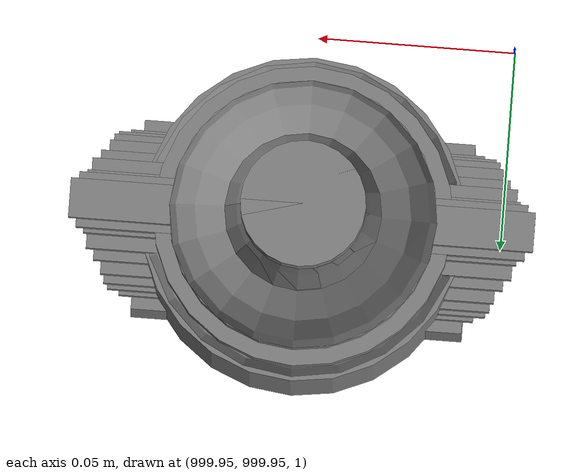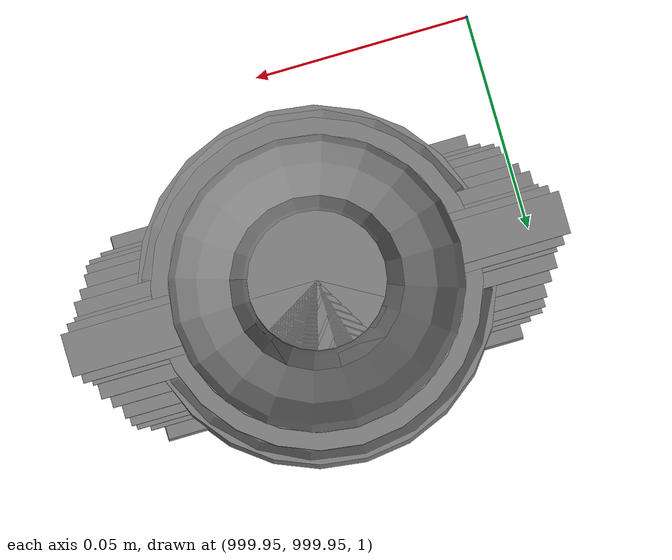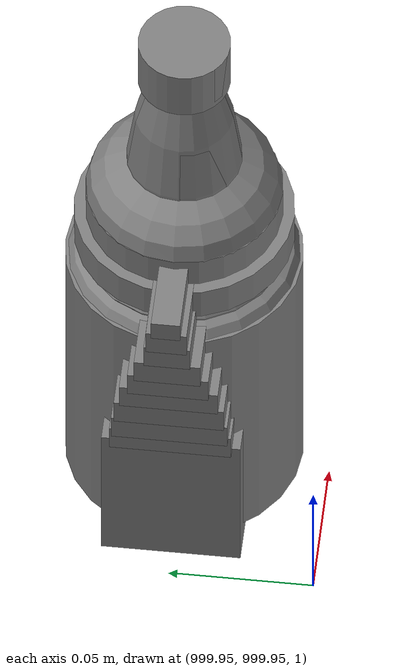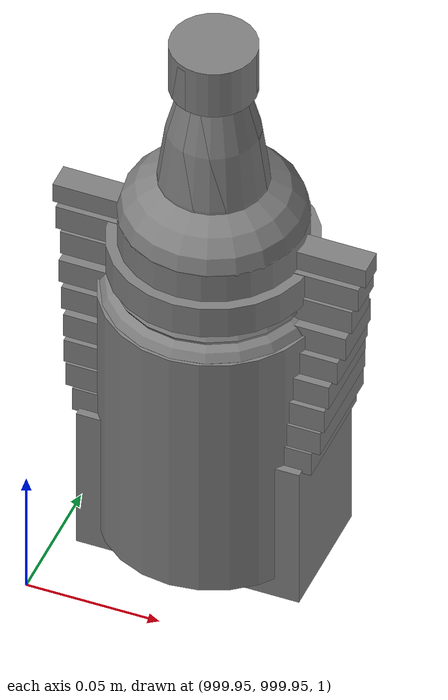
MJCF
<mujoco>
    <option gravity="0.000000000 0.000000000 -9.810000420" timestep="0.0166666" integrator="implicitfast" density="1.225" viscosity="1.8000001e-05" noslip_iterations="10" iterations="100" sdf_iterations="50">
        <flag multiccd="disable"/>
    </option>
    <size memory="1000M"/>
    <compiler coordinate="local"/>
    <worldbody>
        <light cutoff="30" pos="0 1 1" dir="0 -1 -2"/>
        <light cutoff="30" pos="0 -1 1" dir="0 1 -2"/>
        <body pos="-2.436573029 6.404376507 0.137849092" euler="0.000000000 0.000000000 0.000000000" name="openloong_gripper_2f85_fix_base_usda_shoppingtrolley_01">
            <geom contype="1" conaffinity="1" density="1000" type="box" material="" rgba="0.500000000 0.500000000 0.500000000 1.000000000" solimp="0.899999976 0.949999988 0.001000000" friction="1.000000000 0.005000000 0.000100000" solref="0.020000000 1.000000000" margin="0" condim="3" group="0" pos="-0.169898406 -0.178061336 0.864131629" quat="0.916343808 -0.400392294 -0.000000045 0.000000030" size="0.017999999 0.022499999 0.089999996" name="openloong_gripper_2f85_fix_base_usda_geom_3A959429_4941_48AF_A9DA_0D87274571BE"/>
            <geom contype="1" conaffinity="1" density="1000" type="box" material="" rgba="0.500000000 0.500000000 0.500000000 1.000000000" solimp="0.899999976 0.949999988 0.001000000" friction="1.000000000 0.005000000 0.000100000" solref="0.020000000 1.000000000" margin="0" condim="3" group="0" pos="-0.107458733 0.238907143 0.911498845" quat="0.634576976 0.622505128 -0.330067992 -0.317575932" size="0.017999999 0.022499999 0.035999998" name="openloong_gripper_2f85_fix_base_usda_geom_87C32A71_8F42_49F9_9268_79BB2F3D91BB"/>
            <geom contype="1" conaffinity="1" density="1000" type="box" material="" rgba="0.500000000 0.500000000 0.500000000 1.000000000" solimp="0.899999976 0.949999988 0.001000000" friction="1.000000000 0.005000000 0.000100000" solref="0.020000000 1.000000000" margin="0" condim="3" group="0" pos="-0.005004787 0.248085022 0.912686050" quat="1.000000000 0.000000000 0.000000000 0.000000000" size="0.107999995 0.022499999 0.022499999" name="openloong_gripper_2f85_fix_base_usda_geom_EC4AB7C1_82FD_421E_A5BA_979A1BD61907"/>
            <geom contype="1" conaffinity="1" density="1000" type="box" material="" rgba="0.500000000 0.500000000 0.500000000 1.000000000" solimp="0.899999976 0.949999988 0.001000000" friction="1.000000000 0.005000000 0.000100000" solref="0.020000000 1.000000000" margin="0" condim="3" group="0" pos="0.131482959 -0.182533979 0.598989725" quat="0.996607125 0.055331629 0.059003670 0.015205893" size="0.013499999 0.287999988 0.053999998" name="openloong_gripper_2f85_fix_base_usda_geom_41A4AD13_B3F2_4C39_8749_DDBF93C3568A"/>
            <geom contype="1" conaffinity="1" density="1000" type="box" material="" rgba="0.500000000 0.500000000 0.500000000 1.000000000" solimp="0.899999976 0.949999988 0.001000000" friction="1.000000000 0.005000000 0.000100000" solref="0.020000000 1.000000000" margin="0" condim="3" group="0" pos="-0.000005364 0.100332208 0.734785020" quat="0.999668717 0.025737956 -0.000000010 0.000000000" size="0.135000005 0.019800000 0.152999997" name="openloong_gripper_2f85_fix_base_usda_geom_37B13D62_4B80_42D5_A999_ADCDB906D94D"/>
            <geom contype="1" conaffinity="1" density="1000" type="box" material="" rgba="0.500000000 0.500000000 0.500000000 1.000000000" solimp="0.899999976 0.949999988 0.001000000" friction="1.000000000 0.005000000 0.000100000" solref="0.020000000 1.000000000" margin="0" condim="3" group="0" pos="-0.126757339 -0.182533979 0.598989725" quat="0.996607184 0.055331606 -0.059003651 -0.015205891" size="0.013499999 0.287999988 0.053999998" name="openloong_gripper_2f85_fix_base_usda_geom_5CCC4833_9024_45C2_B2E7_98291259242B"/>
            <geom contype="1" conaffinity="1" density="1000" type="box" material="" rgba="0.500000000 0.500000000 0.500000000 1.000000000" solimp="0.899999976 0.949999988 0.001000000" friction="1.000000000 0.005000000 0.000100000" solref="0.020000000 1.000000000" margin="0" condim="3" group="0" pos="-0.134013891 0.200098798 0.912192523" quat="0.694057047 0.679413557 -0.172947660 -0.163618833" size="0.017999999 0.022499999 0.035999998" name="openloong_gripper_2f85_fix_base_usda_geom_DF9ADC86_F44D_4FB1_ACC6_4710EEA55EDB"/>
            <geom contype="1" conaffinity="1" density="1000" type="box" material="" rgba="0.500000000 0.500000000 0.500000000 1.000000000" solimp="0.899999976 0.949999988 0.001000000" friction="1.000000000 0.005000000 0.000100000" solref="0.020000000 1.000000000" margin="0" condim="3" group="0" pos="0.141839072 -0.191051379 0.702451229" quat="0.997147262 0.056065105 0.045779929 0.021407485" size="0.013499999 0.287999988 0.053999998" name="openloong_gripper_2f85_fix_base_usda_geom_0AACA424_11AB_4463_8C46_018BE6078D63"/>
            <geom contype="1" conaffinity="1" density="1000" type="box" material="" rgba="0.500000000 0.500000000 0.500000000 1.000000000" solimp="0.899999976 0.949999988 0.001000000" friction="1.000000000 0.005000000 0.000100000" solref="0.020000000 1.000000000" margin="0" condim="3" group="0" pos="-0.135714188 -0.191051379 0.694841146" quat="0.997147322 0.056064609 -0.045779683 -0.021407485" size="0.013499999 0.287999988 0.053999998" name="openloong_gripper_2f85_fix_base_usda_geom_884312BD_979F_43AA_82C9_A1BD0AA65738"/>
            <geom contype="1" conaffinity="1" density="1000" type="box" material="" rgba="0.500000000 0.500000000 0.500000000 1.000000000" solimp="0.899999976 0.949999988 0.001000000" friction="1.000000000 0.005000000 0.000100000" solref="0.020000000 1.000000000" margin="0" condim="3" group="0" pos="-0.000004721 -0.174527690 0.560063601" quat="0.996704638 0.081116498 -0.000000004 0.000000000" size="0.126000002 0.287999988 0.009000000" name="openloong_gripper_2f85_fix_base_usda_geom_1F331C70_F660_481B_9025_B47F897C9A95"/>
            <geom contype="1" conaffinity="1" density="1000" type="box" material="" rgba="0.500000000 0.500000000 0.500000000 1.000000000" solimp="0.899999976 0.949999988 0.001000000" friction="1.000000000 0.005000000 0.000100000" solref="0.020000000 1.000000000" margin="0" condim="3" group="0" pos="0.134013891 0.200098798 0.912192523" quat="0.692574680 -0.680924535 -0.166899428 0.169783980" size="0.017999999 0.022499999 0.035999998" name="openloong_gripper_2f85_fix_base_usda_geom_82083E4E_2FE8_48FD_8190_EE4F9B212EBA"/>
            <geom contype="1" conaffinity="1" density="1000" type="box" material="" rgba="0.500000000 0.500000000 0.500000000 1.000000000" solimp="0.899999976 0.949999988 0.001000000" friction="1.000000000 0.005000000 0.000100000" solref="0.020000000 1.000000000" margin="0" condim="3" group="0" pos="-0.012634277 -0.174527690 -0.088243507" quat="1.000000000 0.000000000 -0.000000004 0.000000000" size="0.135000005 0.287999988 0.044999998" name="openloong_gripper_2f85_fix_base_usda_geom_7EFBF856_476F_40AB_BC20_93E9572BE250"/>
            <geom contype="1" conaffinity="1" density="1000" type="box" material="" rgba="0.500000000 0.500000000 0.500000000 1.000000000" solimp="0.899999976 0.949999988 0.001000000" friction="1.000000000 0.005000000 0.000100000" solref="0.020000000 1.000000000" margin="0" condim="3" group="0" pos="-0.142927840 -0.199506134 0.784674108" quat="0.998421252 0.016904408 -0.027109101 -0.046199299" size="0.013499999 0.305999994 0.063000001" name="openloong_gripper_2f85_fix_base_usda_geom_6431B549_CAB6_46E6_BED1_DB64B38A94ED"/>
            <geom contype="1" conaffinity="1" density="1000" type="box" material="" rgba="0.500000000 0.500000000 0.500000000 1.000000000" solimp="0.899999976 0.949999988 0.001000000" friction="1.000000000 0.005000000 0.000100000" solref="0.020000000 1.000000000" margin="0" condim="3" group="0" pos="-0.169898406 -0.043119621 0.915120542" quat="0.687021017 0.726584017 -0.005590606 -0.006832919" size="0.017999999 0.022499999 0.089999996" name="openloong_gripper_2f85_fix_base_usda_geom_A2C5C4B9_4045_4073_92FB_8F97EA582A26"/>
            <geom contype="1" conaffinity="1" density="1000" type="box" material="" rgba="0.500000000 0.500000000 0.500000000 1.000000000" solimp="0.899999976 0.949999988 0.001000000" friction="1.000000000 0.005000000 0.000100000" solref="0.020000000 1.000000000" margin="0" condim="3" group="0" pos="-0.000006008 -0.484932661 0.670727849" quat="0.997585475 0.069449045 -0.000000004 -0.000000089" size="0.179999992 0.013499999 0.170999989" name="openloong_gripper_2f85_fix_base_usda_geom_DFDB1904_6D31_4C26_A32C_A3718D41740F"/>
            <geom contype="1" conaffinity="1" density="1000" type="box" material="" rgba="0.500000000 0.500000000 0.500000000 1.000000000" solimp="0.899999976 0.949999988 0.001000000" friction="1.000000000 0.005000000 0.000100000" solref="0.020000000 1.000000000" margin="0" condim="3" group="0" pos="0.160832971 0.103427693 0.910528183" quat="0.711112797 -0.700149298 -0.042821646 0.047705106" size="0.017999999 0.022499999 0.071999997" name="openloong_gripper_2f85_fix_base_usda_geom_6758823C_029D_41CD_9995_D90C6C3C1714"/>
            <geom contype="1" conaffinity="1" density="1000" type="box" material="" rgba="0.500000000 0.500000000 0.500000000 1.000000000" solimp="0.899999976 0.949999988 0.001000000" friction="1.000000000 0.005000000 0.000100000" solref="0.020000000 1.000000000" margin="0" condim="3" group="0" pos="-0.160832763 0.103427693 0.910528183" quat="0.711469591 0.699786782 -0.048386075 -0.042050660" size="0.017999999 0.022499999 0.071999997" name="openloong_gripper_2f85_fix_base_usda_geom_FD3E3B99_47F4_4036_9E17_7EF0B85090E3"/>
            <geom contype="1" conaffinity="1" density="1000" type="box" material="" rgba="0.500000000 0.500000000 0.500000000 1.000000000" solimp="0.899999976 0.949999988 0.001000000" friction="1.000000000 0.005000000 0.000100000" solref="0.020000000 1.000000000" margin="0" condim="3" group="0" pos="0.169898629 -0.178061336 0.864131629" quat="0.916343808 -0.400392294 -0.000000045 0.000000030" size="0.017999999 0.022499999 0.089999996" name="openloong_gripper_2f85_fix_base_usda_geom_023D4922_BB2D_4FF7_8B99_F5761F062EA8"/>
            <geom contype="1" conaffinity="1" density="1000" type="box" material="" rgba="0.500000000 0.500000000 0.500000000 1.000000000" solimp="0.899999976 0.949999988 0.001000000" friction="1.000000000 0.005000000 0.000100000" solref="0.020000000 1.000000000" margin="0" condim="3" group="0" pos="0.103667587 0.233050480 0.912927270" quat="0.634205043 -0.622199059 -0.324503720 0.324576139" size="0.017999999 0.022499999 0.035999998" name="openloong_gripper_2f85_fix_base_usda_geom_F4F11376_1452_4E2F_9A72_F26442093A65"/>
            <geom contype="1" conaffinity="1" density="1000" type="box" material="" rgba="0.500000000 0.500000000 0.500000000 1.000000000" solimp="0.899999976 0.949999988 0.001000000" friction="1.000000000 0.005000000 0.000100000" solref="0.020000000 1.000000000" margin="0" condim="3" group="0" pos="0.169898629 -0.043119621 0.915120542" quat="0.687029123 -0.726576388 -0.006509603 0.005963952" size="0.017999999 0.022499999 0.089999996" name="openloong_gripper_2f85_fix_base_usda_geom_52F31E02_BDDD_4E0A_B152_79C7915C8A50"/>
            <geom contype="1" conaffinity="1" density="1000" type="box" material="" rgba="0.500000000 0.500000000 0.500000000 1.000000000" solimp="0.899999976 0.949999988 0.001000000" friction="1.000000000 0.005000000 0.000100000" solref="0.020000000 1.000000000" margin="0" condim="3" group="0" pos="0.148195267 -0.199506566 0.782808602" quat="0.998808920 0.017156634 0.026950166 0.036880098" size="0.013499999 0.305999994 0.063000001" name="openloong_gripper_2f85_fix_base_usda_geom_71EF9CBC_3B1C_49F1_8D14_BCEA5E258FAD"/>
            <freejoint name="openloong_gripper_2f85_fix_base_usda_shoppingtrolley_01_joint"/>
            <site size="0.005000000 0.005000000 0.005000000" rgba="0.500000000 0.500000000 0.500000000 1.000000000" pos="0.000000000 0.000000000 0.000000000" quat="1.000000000 0.000000000 0.000000000 0.000000000" group="0" type="sphere" name="openloong_gripper_2f85_fix_base_usda_shoppingtrolley_01"/>
        </body>
        <body pos="1000.000000000 1000.000000000 1.000000000" euler="0.000000000 0.000000000 0.000000000" name="openloong_gripper_2f85_fix_base_usda_can">
            <geom contype="1" conaffinity="1" density="1000" type="cylinder" material="" rgba="0.500000000 0.500000000 0.500000000 1.000000000" solimp="0.899999976 0.949999988 0.001000000" friction="1.000000000 0.005000000 0.000100000" solref="0.020000000 1.000000000" margin="0" condim="3" group="0" pos="0.000000000 0.000000000 0.079676986" quat="1.000000000 0.000000000 0.000000000 0.000000000" size="0.034000002 0.071999997 1.000000000" name="openloong_gripper_2f85_fix_base_usda_geom_050DDD89_0D67_4347_87A7_CF3FF79CDD16"/>
            <geom contype="1" conaffinity="1" density="1000" type="ellipsoid" material="" rgba="0.500000000 0.500000000 0.500000000 1.000000000" solimp="0.899999976 0.949999988 0.001000000" friction="1.000000000 0.005000000 0.000100000" solref="0.020000000 1.000000000" margin="0" condim="3" group="0" pos="0.000000000 0.000000000 0.151854277" quat="1.000000000 0.000000000 0.000000000 0.000000000" size="0.034000002 0.034000002 0.020000000" name="openloong_gripper_2f85_fix_base_usda_geom_4E051A32_B954_4723_8FE0_7172098C69AF"/>
            <geom contype="1" conaffinity="1" density="1000" type="box" material="" rgba="0.500000000 0.500000000 0.500000000 1.000000000" solimp="0.899999976 0.949999988 0.001000000" friction="1.000000000 0.005000000 0.000100000" solref="0.020000000 1.000000000" margin="0" condim="3" group="0" pos="0.000000000 0.000000000 0.004777670" quat="1.000000000 0.000000000 0.000000000 0.000000000" size="0.020000000 0.020000000 0.005000000" name="openloong_gripper_2f85_fix_base_usda_geom_F3A150A1_B58F_4A54_946F_6D42C9534BF9"/>
            <freejoint name="openloong_gripper_2f85_fix_base_usda_can_joint"/>
            <site size="0.005000000 0.005000000 0.005000000" rgba="0.500000000 0.500000000 0.500000000 1.000000000" pos="0.000000000 0.000000000 0.000000000" quat="1.000000000 0.000000000 0.000000000 0.000000000" group="0" type="sphere" name="openloong_gripper_2f85_fix_base_usda_cansite"/>
        </body>
        <body pos="-1.982231140 6.360698700 1.692813635" euler="82.389839172 60.700508118 -127.896240234" mocap="true" name="spotlight4_SpotLight"/>
        <body pos="1000.000000000 1000.000000000 1.000000000" euler="0.000000000 0.000000000 0.000000000" name="openloong_gripper_2f85_fix_base_usda_bottle_blue">
            <geom contype="1" conaffinity="1" density="1000" type="ellipsoid" material="" rgba="0.500000000 0.500000000 0.500000000 1.000000000" solimp="0.899999976 0.949999988 0.001000000" friction="1.000000000 0.005000000 0.000100000" solref="0.020000000 1.000000000" margin="0" condim="3" group="0" pos="0.000000000 0.000000000 0.118920922" quat="1.000000000 0.000000000 0.000000000 0.000000000" size="0.030999999 0.030999999 0.029999999" name="openloong_gripper_2f85_fix_base_usda_geom_5369E21A_3268_453E_A552_BD2EA777479E"/>
            <geom contype="1" conaffinity="1" density="1000" type="box" material="" rgba="0.500000000 0.500000000 0.500000000 1.000000000" solimp="0.899999976 0.949999988 0.001000000" friction="1.000000000 0.005000000 0.000100000" solref="0.020000000 1.000000000" margin="0" condim="3" group="0" pos="0.000000000 0.000000000 0.002164602" quat="1.000000000 0.000000000 0.000000000 0.000000000" size="0.020000000 0.020000000 0.003000000" name="openloong_gripper_2f85_fix_base_usda_geom_9BA0410C_92BE_4D9E_A6F7_0F4AFCEBE951"/>
            <geom contype="1" conaffinity="1" density="1000" type="cylinder" material="" rgba="0.500000000 0.500000000 0.500000000 1.000000000" solimp="0.899999976 0.949999988 0.001000000" friction="1.000000000 0.005000000 0.000100000" solref="0.020000000 1.000000000" margin="0" condim="3" group="0" pos="0.000000000 -0.000366211 0.060859680" quat="1.000000000 0.000000000 0.000000000 0.000000000" size="0.030999999 0.057999998 1.000000000" name="openloong_gripper_2f85_fix_base_usda_geom_6C55E1FA_7B42_4E0E_8B32_FBF3A5F8B284"/>
            <geom contype="1" conaffinity="1" density="1000" type="cylinder" material="" rgba="0.500000000 0.500000000 0.500000000 1.000000000" solimp="0.899999976 0.949999988 0.001000000" friction="1.000000000 0.005000000 0.000100000" solref="0.020000000 1.000000000" margin="0" condim="3" group="0" pos="0.000000000 0.000000000 0.220594406" quat="1.000000000 0.000000000 0.000000000 0.000000000" size="0.016000001 0.010000000 1.000000000" name="openloong_gripper_2f85_fix_base_usda_geom_01E82D58_FA53_46DE_A746_D178C630B25C"/>
            <geom contype="1" conaffinity="1" density="1000" type="ellipsoid" material="" rgba="0.500000000 0.500000000 0.500000000 1.000000000" solimp="0.899999976 0.949999988 0.001000000" friction="1.000000000 0.005000000 0.000100000" solref="0.020000000 1.000000000" margin="0" condim="3" group="0" pos="0.000000000 0.000000000 0.144259930" quat="1.000000000 0.000000000 0.000000000 0.000000000" size="0.021000000 0.021000000 0.079999998" name="openloong_gripper_2f85_fix_base_usda_geom_36D9ED09_4758_4AAB_B8E2_A7AA9481EDB9"/>
            <freejoint name="openloong_gripper_2f85_fix_base_usda_bottle_blue_joint"/>
            <site size="0.005000000 0.005000000 0.005000000" rgba="0.500000000 0.500000000 0.500000000 1.000000000" pos="0.000000000 0.000000000 0.000000000" quat="0.999961913 0.008726535 0.000000000 0.000000000" group="0" type="sphere" name="openloong_gripper_2f85_fix_base_usda_bottle_bluesite"/>
        </body>
        <body pos="1000.000000000 1000.000000000 1.000000000" euler="0.000000000 0.000000000 0.000000000" name="openloong_gripper_2f85_fix_base_usda_jar_01">
            <geom contype="1" conaffinity="1" density="1000" type="box" material="" rgba="0.500000000 0.500000000 0.500000000 1.000000000" solimp="0.899999976 0.949999988 0.001000000" friction="1.000000000 0.005000000 0.000100000" solref="0.020000000 1.000000000" margin="0" condim="3" group="0" pos="0.000000000 0.000000000 0.006158113" quat="1.000000000 0.000000000 0.000000000 0.000000000" size="0.020000000 0.020000000 0.005000000" name="openloong_gripper_2f85_fix_base_usda_geom_510C5409_E8D7_4877_A1ED_B4C2A18C27C9"/>
            <geom contype="1" conaffinity="1" density="1000" type="cylinder" material="" rgba="0.500000000 0.500000000 0.500000000 1.000000000" solimp="0.899999976 0.949999988 0.001000000" friction="1.000000000 0.005000000 0.000100000" solref="0.020000000 1.000000000" margin="0" condim="3" group="0" pos="0.000000000 0.000000000 0.062744498" quat="1.000000000 0.000000000 0.000000000 0.000000000" size="0.041000001 0.052999999 1.000000000" name="openloong_gripper_2f85_fix_base_usda_geom_4F77DC7C_B110_4F55_BCF4_93E89AC50A9E"/>
            <geom contype="1" conaffinity="1" density="1000" type="ellipsoid" material="" rgba="0.500000000 0.500000000 0.500000000 1.000000000" solimp="0.899999976 0.949999988 0.001000000" friction="1.000000000 0.005000000 0.000100000" solref="0.020000000 1.000000000" margin="0" condim="3" group="0" pos="0.000000000 0.000000000 0.122252703" quat="1.000000000 0.000000000 0.000000000 0.000000000" size="0.035999998 0.035999998 0.010000000" name="openloong_gripper_2f85_fix_base_usda_geom_7A1E6CC4_19BD_4D1C_8AF6_FA977A0EA3AA"/>
            <geom contype="1" conaffinity="1" density="1000" type="cylinder" material="" rgba="0.500000000 0.500000000 0.500000000 1.000000000" solimp="0.899999976 0.949999988 0.001000000" friction="1.000000000 0.005000000 0.000100000" solref="0.020000000 1.000000000" margin="0" condim="3" group="0" pos="0.000000000 0.000000000 0.015747190" quat="1.000000000 0.000000000 0.000000000 0.000000000" size="0.035000000 0.010000000 1.000000000" name="openloong_gripper_2f85_fix_base_usda_geom_8F1925FA_3EBE_43C7_8958_319883096A1B"/>
            <geom contype="1" conaffinity="1" density="1000" type="ellipsoid" material="" rgba="0.500000000 0.500000000 0.500000000 1.000000000" solimp="0.899999976 0.949999988 0.001000000" friction="1.000000000 0.005000000 0.000100000" solref="0.020000000 1.000000000" margin="0" condim="3" group="0" pos="0.000000000 0.000000000 0.115815401" quat="1.000000000 0.000000000 0.000000000 0.000000000" size="0.039999999 0.039999999 0.010000000" name="openloong_gripper_2f85_fix_base_usda_geom_6CCB526B_AA55_4363_B5D4_F1097B490069"/>
            <geom contype="1" conaffinity="1" density="1000" type="cylinder" material="" rgba="0.500000000 0.500000000 0.500000000 1.000000000" solimp="0.899999976 0.949999988 0.001000000" friction="1.000000000 0.005000000 0.000100000" solref="0.020000000 1.000000000" margin="0" condim="3" group="0" pos="0.000000000 0.000000000 0.133183479" quat="1.000000000 0.000000000 0.000000000 0.000000000" size="0.037999999 0.006500000 1.000000000" name="openloong_gripper_2f85_fix_base_usda_geom_CF2DA420_EDAD_41CF_AFC6_2FA8C7FD15D4"/>
            <freejoint name="openloong_gripper_2f85_fix_base_usda_jar_01_joint"/>
            <site size="0.005000000 0.005000000 0.005000000" rgba="0.500000000 0.500000000 0.500000000 1.000000000" pos="0.000000000 0.000000000 0.000000000" quat="1.000000000 0.000000000 0.000000000 0.000000000" group="0" type="sphere" name="openloong_gripper_2f85_fix_base_usda_jar_01site"/>
        </body>
        <body pos="1000.000000000 1000.000000000 1.000000000" euler="0.000000000 0.000000000 0.000000000" name="openloong_gripper_2f85_fix_base_usda_bottle_red">
            <geom contype="1" conaffinity="1" density="1000" type="ellipsoid" material="" rgba="0.500000000 0.500000000 0.500000000 1.000000000" solimp="0.899999976 0.949999988 0.001000000" friction="1.000000000 0.005000000 0.000100000" solref="0.020000000 1.000000000" margin="0" condim="3" group="0" pos="0.000000000 0.000000000 0.144284487" quat="1.000000000 0.000000000 0.000000000 0.000000000" size="0.021000000 0.021000000 0.079999998" name="openloong_gripper_2f85_fix_base_usda_geom_4483806C_AF13_4A74_AC41_F0F22B787C59"/>
            <geom contype="1" conaffinity="1" density="1000" type="cylinder" material="" rgba="0.500000000 0.500000000 0.500000000 1.000000000" solimp="0.899999976 0.949999988 0.001000000" friction="1.000000000 0.005000000 0.000100000" solref="0.020000000 1.000000000" margin="0" condim="3" group="0" pos="0.000000000 0.000000000 0.220618963" quat="1.000000000 0.000000000 0.000000000 0.000000000" size="0.016000001 0.010000000 1.000000000" name="openloong_gripper_2f85_fix_base_usda_geom_F6DED92C_75AE_43D9_B1E6_5D8F5BD55772"/>
            <geom contype="1" conaffinity="1" density="1000" type="ellipsoid" material="" rgba="0.500000000 0.500000000 0.500000000 1.000000000" solimp="0.899999976 0.949999988 0.001000000" friction="1.000000000 0.005000000 0.000100000" solref="0.020000000 1.000000000" margin="0" condim="3" group="0" pos="0.000000000 0.000000000 0.118945479" quat="1.000000000 0.000000000 0.000000000 0.000000000" size="0.030999999 0.030999999 0.029999999" name="openloong_gripper_2f85_fix_base_usda_geom_50703A83_95CD_4152_9ECF_71DA0EBD64EF"/>
            <geom contype="1" conaffinity="1" density="1000" type="box" material="" rgba="0.500000000 0.500000000 0.500000000 1.000000000" solimp="0.899999976 0.949999988 0.001000000" friction="1.000000000 0.005000000 0.000100000" solref="0.020000000 1.000000000" margin="0" condim="3" group="0" pos="0.000000000 0.000000000 0.002189159" quat="1.000000000 0.000000000 0.000000000 0.000000000" size="0.020000000 0.020000000 0.003000000" name="openloong_gripper_2f85_fix_base_usda_geom_0F927FA5_3B00_49F1_B0F8_1E3B36828109"/>
            <geom contype="1" conaffinity="1" density="1000" type="cylinder" material="" rgba="0.500000000 0.500000000 0.500000000 1.000000000" solimp="0.899999976 0.949999988 0.001000000" friction="1.000000000 0.005000000 0.000100000" solref="0.020000000 1.000000000" margin="0" condim="3" group="0" pos="0.000000000 -0.000366211 0.060884237" quat="1.000000000 0.000000000 0.000000000 0.000000000" size="0.030999999 0.057999998 1.000000000" name="openloong_gripper_2f85_fix_base_usda_geom_050AB5C3_BFE9_47B3_9037_9AEB3CD3CBCA"/>
            <freejoint name="openloong_gripper_2f85_fix_base_usda_bottle_red_joint"/>
            <site size="0.005000000 0.005000000 0.005000000" rgba="0.500000000 0.500000000 0.500000000 1.000000000" pos="0.000000000 0.000000000 0.000000000" quat="0.999961913 0.008726535 0.000000000 0.000000000" group="0" type="sphere" name="openloong_gripper_2f85_fix_base_usda_bottle_redsite"/>
        </body>
        <body pos="-2.007819653 6.529432297 1.801786184" euler="15.627361298 -26.974813461 -67.468734741" mocap="true" name="spotlight5_SpotLight"/>
        <body pos="1000.000000000 1000.000000000 1.000000000" euler="0.000000000 0.000000000 0.000000000" name="openloong_gripper_2f85_fix_base_usda_salt">
            <geom contype="1" conaffinity="1" density="1000" type="box" material="" rgba="0.500000000 0.500000000 0.500000000 1.000000000" solimp="0.899999976 0.949999988 0.001000000" friction="1.000000000 0.005000000 0.000100000" solref="0.020000000 1.000000000" margin="0" condim="3" group="0" pos="0.000305176 0.000000000 0.084862232" quat="1.000000000 0.000000000 0.000000000 0.000000000" size="0.048999999 0.018999999 0.005000000" name="openloong_gripper_2f85_fix_base_usda_geom_EECD06E9_1A30_4521_BE68_CAA4CAD4B674"/>
            <geom contype="1" conaffinity="1" density="1000" type="box" material="" rgba="0.500000000 0.500000000 0.500000000 1.000000000" solimp="0.899999976 0.949999988 0.001000000" friction="1.000000000 0.005000000 0.000100000" solref="0.020000000 1.000000000" margin="0" condim="3" group="0" pos="0.000305176 0.000000000 0.104564309" quat="1.000000000 0.000000000 0.000000000 0.000000000" size="0.052000001 0.014000000 0.005000000" name="openloong_gripper_2f85_fix_base_usda_geom_4CC2BAA5_6287_4A94_A9DB_F288D7A63FE1"/>
            <geom contype="1" conaffinity="1" density="1000" type="box" material="" rgba="0.500000000 0.500000000 0.500000000 1.000000000" solimp="0.899999976 0.949999988 0.001000000" friction="1.000000000 0.005000000 0.000100000" solref="0.020000000 1.000000000" margin="0" condim="3" group="0" pos="0.000305176 0.000000000 0.114487171" quat="1.000000000 0.000000000 0.000000000 0.000000000" size="0.054000001 0.011500000 0.005000000" name="openloong_gripper_2f85_fix_base_usda_geom_4C98CB2D_B047_4B50_9A7E_C333E938734F"/>
            <geom contype="1" conaffinity="1" density="1000" type="box" material="" rgba="0.500000000 0.500000000 0.500000000 1.000000000" solimp="0.899999976 0.949999988 0.001000000" friction="1.000000000 0.005000000 0.000100000" solref="0.020000000 1.000000000" margin="0" condim="3" group="0" pos="0.000305176 0.000000000 0.075103164" quat="1.000000000 0.000000000 0.000000000 0.000000000" size="0.048000000 0.020000000 0.005000000" name="openloong_gripper_2f85_fix_base_usda_geom_1FBA6BA4_65B9_40F0_834A_7C4C20EF370F"/>
            <geom contype="1" conaffinity="1" density="1000" type="box" material="" rgba="0.500000000 0.500000000 0.500000000 1.000000000" solimp="0.899999976 0.949999988 0.001000000" friction="1.000000000 0.005000000 0.000100000" solref="0.020000000 1.000000000" margin="0" condim="3" group="0" pos="0.000305176 0.000000000 0.134892464" quat="1.000000000 0.000000000 0.000000000 0.000000000" size="0.057000000 0.007000000 0.005000000" name="openloong_gripper_2f85_fix_base_usda_geom_A3CA28C5_CD49_4C8F_BCDE_784B6F0889EB"/>
            <geom contype="1" conaffinity="1" density="1000" type="box" material="" rgba="0.500000000 0.500000000 0.500000000 1.000000000" solimp="0.899999976 0.949999988 0.001000000" friction="1.000000000 0.005000000 0.000100000" solref="0.020000000 1.000000000" margin="0" condim="3" group="0" pos="0.000305176 0.000000000 0.094920278" quat="1.000000000 0.000000000 0.000000000 0.000000000" size="0.050000001 0.017000001 0.005000000" name="openloong_gripper_2f85_fix_base_usda_geom_5DB1537D_AA51_4E37_BC52_52A90A055783"/>
            <geom contype="1" conaffinity="1" density="1000" type="box" material="" rgba="0.500000000 0.500000000 0.500000000 1.000000000" solimp="0.899999976 0.949999988 0.001000000" friction="1.000000000 0.005000000 0.000100000" solref="0.020000000 1.000000000" margin="0" condim="3" group="0" pos="0.000305176 0.000000000 0.065204859" quat="1.000000000 0.000000000 0.000000000 0.000000000" size="0.045000002 0.021000000 0.005000000" name="openloong_gripper_2f85_fix_base_usda_geom_D87FA578_4E5E_484B_ABB1_85B02D5DD821"/>
            <geom contype="1" conaffinity="1" density="1000" type="box" material="" rgba="0.500000000 0.500000000 0.500000000 1.000000000" solimp="0.899999976 0.949999988 0.001000000" friction="1.000000000 0.005000000 0.000100000" solref="0.020000000 1.000000000" margin="0" condim="3" group="0" pos="0.000305176 0.000000000 0.144135714" quat="1.000000000 0.000000000 0.000000000 0.000000000" size="0.059000000 0.005000000 0.004000000" name="openloong_gripper_2f85_fix_base_usda_geom_172441C1_B629_4B8A_96A2_2542F3DFEA93"/>
            <geom contype="1" conaffinity="1" density="1000" type="box" material="" rgba="0.500000000 0.500000000 0.500000000 1.000000000" solimp="0.899999976 0.949999988 0.001000000" friction="1.000000000 0.005000000 0.000100000" solref="0.020000000 1.000000000" margin="0" condim="3" group="0" pos="0.000000000 0.000000000 0.031593561" quat="1.000000000 0.000000000 0.000000000 0.000000000" size="0.041999999 0.024000000 0.029999999" name="openloong_gripper_2f85_fix_base_usda_geom_8E832A3F_AE5E_4DA3_8AE8_90EBABA5C368"/>
            <geom contype="1" conaffinity="1" density="1000" type="box" material="" rgba="0.500000000 0.500000000 0.500000000 1.000000000" solimp="0.899999976 0.949999988 0.001000000" friction="1.000000000 0.005000000 0.000100000" solref="0.020000000 1.000000000" margin="0" condim="3" group="0" pos="0.000305176 0.000000000 0.124608755" quat="1.000000000 0.000000000 0.000000000 0.000000000" size="0.055000000 0.008000000 0.005000000" name="openloong_gripper_2f85_fix_base_usda_geom_571DDA7F_D919_4E6D_AB98_4FC851A06F10"/>
            <freejoint name="openloong_gripper_2f85_fix_base_usda_salt_joint"/>
            <site size="0.005000000 0.005000000 0.005000000" rgba="0.500000000 0.500000000 0.500000000 1.000000000" pos="0.000000000 0.000000000 0.000000000" quat="1.000000000 0.000000000 0.000000000 0.000000000" group="0" type="sphere" name="openloong_gripper_2f85_fix_base_usda_saltsite"/>
        </body>
        <body pos="-2.129305601 5.976374149 1.836662173" euler="-106.765701294 -68.543571472 104.769142151" mocap="true" name="spotlight2_SpotLight"/>
        <body pos="0.000000000 0.000000000 0.000000000" euler="0.000000000 0.000000000 0.000000000" name=" Static Objects_ Static Objects">
            <geom contype="1" conaffinity="1" density="1000" type="box" material="" rgba="0.500000000 0.500000000 0.500000000 1.000000000" solimp="0.899999976 0.949999988 0.001000000" friction="1.000000000 0.005000000 0.000100000" solref="0.020000000 1.000000000" margin="0" condim="3" group="0" pos="-3.101639986 6.150595188 1.018643856" quat="1.000000000 0.000000000 0.000000000 0.000000000" size="0.050000001 0.579999983 1.019999981" name=" Static Objects_geom_0240412F_D9B9_462C_8C82_257ECE08B3E2"/>
            <geom contype="1" conaffinity="1" density="1000" type="box" material="" rgba="0.500000000 0.500000000 0.500000000 1.000000000" solimp="0.899999976 0.949999988 0.001000000" friction="1.000000000 0.005000000 0.000100000" solref="0.020000000 1.000000000" margin="0" condim="3" group="0" pos="-2.825197220 6.153595448 1.115278244" quat="0.707107067 0.000000000 0.000000000 0.707106471" size="0.550000012 0.239999995 0.025000000" name=" Static Objects_geom_889643EF_B178_4000_A8B7_55801973B3F2"/>
            <geom contype="1" conaffinity="1" density="1000" type="box" material="" rgba="0.500000000 0.500000000 0.500000000 1.000000000" solimp="0.899999976 0.949999988 0.001000000" friction="1.000000000 0.005000000 0.000100000" solref="0.020000000 1.000000000" margin="0" condim="3" group="0" pos="-2.825197220 6.153595448 0.097434282" quat="0.707107067 0.000000000 0.000000000 0.707106471" size="0.550000012 0.239999995 0.098999999" name=" Static Objects_geom_05B4CDD7_72DC_41D0_A7E1_8BFB238BB068"/>
            <geom contype="1" conaffinity="1" density="1000" type="box" material="" rgba="0.500000000 0.500000000 0.500000000 1.000000000" solimp="0.899999976 0.949999988 0.001000000" friction="1.000000000 0.005000000 0.000100000" solref="0.020000000 1.000000000" margin="0" condim="3" group="0" pos="-6.293097973 6.153595448 1.114443064" quat="0.707107067 0.000000000 0.000000000 0.707106471" size="0.529999971 3.134999990 0.025000000" name=" Static Objects_geom_64BDE2CB_5D87_456C_B744_119BDA400F63"/>
            <geom contype="1" conaffinity="1" density="1000" type="box" material="" rgba="0.500000000 0.500000000 0.500000000 1.000000000" solimp="0.899999976 0.949999988 0.001000000" friction="1.000000000 0.005000000 0.000100000" solref="0.020000000 1.000000000" margin="0" condim="3" group="0" pos="-6.286010742 6.153595448 0.096129179" quat="0.707107067 0.000000000 0.000000000 0.707106471" size="0.529999971 3.134999990 0.098999999" name=" Static Objects_geom_0175B546_F4C1_4CD2_B597_364759884028"/>
            <geom contype="1" conaffinity="1" density="1000" type="box" material="" rgba="0.500000000 0.500000000 0.500000000 1.000000000" solimp="0.899999976 0.949999988 0.001000000" friction="1.000000000 0.005000000 0.000100000" solref="0.020000000 1.000000000" margin="0" condim="3" group="0" pos="-2.825197220 6.153595448 1.563861728" quat="0.707107067 0.000000000 0.000000000 0.707106471" size="0.550000012 0.239999995 0.025000000" name=" Static Objects_geom_B57741B9_30AD_4C8C_9652_25B6A3B4ED52"/>
            <geom contype="1" conaffinity="1" density="1000" type="box" material="" rgba="0.500000000 0.500000000 0.500000000 1.000000000" solimp="0.899999976 0.949999988 0.001000000" friction="1.000000000 0.005000000 0.000100000" solref="0.020000000 1.000000000" margin="0" condim="3" group="0" pos="-6.311686516 6.153595448 1.018643856" quat="0.707107067 0.000000000 0.000000000 0.707106471" size="0.050000001 3.150000095 1.019999981" name=" Static Objects_geom_86FDA225_8777_4405_9503_E44B30D13609"/>
            <geom contype="1" conaffinity="1" density="1000" type="box" material="" rgba="0.500000000 0.500000000 0.500000000 1.000000000" solimp="0.899999976 0.949999988 0.001000000" friction="1.000000000 0.005000000 0.000100000" solref="0.020000000 1.000000000" margin="0" condim="3" group="0" pos="-2.825197220 6.153595448 0.629031777" quat="0.707107067 0.000000000 0.000000000 0.707106471" size="0.550000012 0.239999995 0.025000000" name=" Static Objects_geom_C6153BE1_B4C9_48B7_B713_52F35ED9DA77"/>
            <geom contype="1" conaffinity="1" density="1000" type="box" material="" rgba="0.500000000 0.500000000 0.500000000 1.000000000" solimp="0.899999976 0.949999988 0.001000000" friction="1.000000000 0.005000000 0.000100000" solref="0.020000000 1.000000000" margin="0" condim="3" group="0" pos="-6.286010742 6.153595448 1.563861728" quat="0.707107067 0.000000000 0.000000000 0.707106471" size="0.529999971 3.134999990 0.025000000" name=" Static Objects_geom_B504EDE5_FE90_47E1_B1FB_9AA451C4C5E8"/>
            <geom contype="1" conaffinity="1" density="1000" type="box" material="" rgba="0.500000000 0.500000000 0.500000000 1.000000000" solimp="0.899999976 0.949999988 0.001000000" friction="1.000000000 0.005000000 0.000100000" solref="0.020000000 1.000000000" margin="0" condim="3" group="0" pos="-6.286010742 6.153595448 0.629031777" quat="0.707107067 0.000000000 0.000000000 0.707106471" size="0.529999971 3.134999990 0.025000000" name=" Static Objects_geom_699FB92A_429A_4B60_AD85_FC0F98F9DDBE"/>
            <geom contype="1" conaffinity="1" density="1000" type="box" material="" rgba="0.500000000 0.500000000 0.500000000 1.000000000" solimp="0.899999976 0.949999988 0.001000000" friction="1.000000000 0.005000000 0.000100000" solref="0.020000000 1.000000000" margin="0" condim="3" group="0" pos="-7.719123363 2.867671013 1.173410416" quat="1.000000000 0.000000000 0.000000000 0.000000000" size="0.250000000 0.250000000 0.079999998" name=" Static Objects_geom_4E0F72CA_EBE7_45FD_8699_C7CB74E5CA5F"/>
            <geom contype="1" conaffinity="1" density="1000" type="box" material="" rgba="0.500000000 0.500000000 0.500000000 1.000000000" solimp="0.899999976 0.949999988 0.001000000" friction="1.000000000 0.005000000 0.000100000" solref="0.020000000 1.000000000" margin="0" condim="3" group="0" pos="-7.408766270 3.088089943 1.776644945" quat="0.928051054 0.000000000 0.000000000 0.372453064" size="0.050000001 0.100000001 0.050000001" name=" Static Objects_geom_E2B18892_0D54_4363_90EB_D3EEFD000FB2"/>
            <geom contype="1" conaffinity="1" density="1000" type="box" material="" rgba="0.500000000 0.500000000 0.500000000 1.000000000" solimp="0.899999976 0.949999988 0.001000000" friction="1.000000000 0.005000000 0.000100000" solref="0.020000000 1.000000000" margin="0" condim="3" group="0" pos="-7.719123363 2.958004713 1.530241251" quat="1.000000000 0.000000000 0.000000000 0.000000000" size="0.250000000 0.159999996 0.280000001" name=" Static Objects_geom_2BE28D8B_914D_4727_972A_47F7E8A04BF3"/>
            <geom contype="1" conaffinity="1" density="1000" type="cylinder" material="" rgba="0.500000000 0.500000000 0.500000000 1.000000000" solimp="0.899999976 0.949999988 0.001000000" friction="1.000000000 0.005000000 0.000100000" solref="0.020000000 1.000000000" margin="0" condim="3" group="0" pos="-7.427312374 3.069516420 1.502544641" quat="0.928051054 0.000000000 0.000000000 0.372453064" size="0.015000000 0.230000004 0.100000001" name=" Static Objects_geom_557ECEDE_D5EA_4575_9BA6_917FCA4AA16C"/>
            <geom contype="1" conaffinity="1" density="1000" type="box" material="" rgba="0.500000000 0.500000000 0.500000000 1.000000000" solimp="0.899999976 0.949999988 0.001000000" friction="1.000000000 0.005000000 0.000100000" solref="0.020000000 1.000000000" margin="0" condim="3" group="0" pos="-7.437745571 3.067511320 1.289965630" quat="1.000000000 0.000000000 0.000000000 0.000000000" size="0.029999999 0.020000000 0.020000000" name=" Static Objects_geom_1A1382C8_A4AC_481B_B6C9_BD6D7A29F7DA"/>
            <geom contype="1" conaffinity="1" density="1000" type="box" material="" rgba="0.500000000 0.500000000 0.500000000 1.000000000" solimp="0.899999976 0.949999988 0.001000000" friction="1.000000000 0.005000000 0.000100000" solref="0.020000000 1.000000000" margin="0" condim="3" group="0" pos="-9.058088303 6.434794426 1.209077358" quat="1.000000000 0.000000000 0.000000000 0.000000000" size="0.250000000 0.100000001 0.070000000" name=" Static Objects_geom_CABF495C_5DAB_4762_ABFE_AC222D427FC3"/>
            <geom contype="1" conaffinity="1" density="1000" type="box" material="" rgba="0.500000000 0.500000000 0.500000000 1.000000000" solimp="0.899999976 0.949999988 0.001000000" friction="1.000000000 0.005000000 0.000100000" solref="0.020000000 1.000000000" margin="0" condim="3" group="0" pos="-7.886891365 6.459744930 0.352518857" quat="1.000000000 0.000000000 0.000000000 0.000000000" size="1.500000000 0.200000003 0.150000006" name=" Static Objects_geom_C5A757FC_EF93_4E20_BB1A_6983776E51D2"/>
            <geom contype="1" conaffinity="1" density="1000" type="box" material="" rgba="0.500000000 0.500000000 0.500000000 1.000000000" solimp="0.899999976 0.949999988 0.001000000" friction="1.000000000 0.005000000 0.000100000" solref="0.020000000 1.000000000" margin="0" condim="3" group="0" pos="-9.237723351 6.464855671 1.209077358" quat="1.000000000 0.000000000 0.000000000 0.000000000" size="0.100000001 0.100000001 0.070000000" name=" Static Objects_geom_AB81F4D4_0FDE_4403_87B5_3279C182B143"/>
            <geom contype="1" conaffinity="1" density="1000" type="box" material="" rgba="0.500000000 0.500000000 0.500000000 1.000000000" solimp="0.899999976 0.949999988 0.001000000" friction="1.000000000 0.005000000 0.000100000" solref="0.020000000 1.000000000" margin="0" condim="3" group="0" pos="-6.924745083 6.362090111 1.214329123" quat="1.000000000 0.000000000 0.000000000 0.000000000" size="0.200000003 0.100000001 0.075000003" name=" Static Objects_geom_6322A9C0_9604_48E8_8A9D_4D8D84C5F975"/>
            <geom contype="1" conaffinity="1" density="1000" type="box" material="" rgba="0.500000000 0.500000000 0.500000000 1.000000000" solimp="0.899999976 0.949999988 0.001000000" friction="1.000000000 0.005000000 0.000100000" solref="0.020000000 1.000000000" margin="0" condim="3" group="0" pos="-4.407354832 6.459744930 1.292199373" quat="1.000000000 0.000000000 0.000000000 0.000000000" size="1.240000010 0.200000003 0.150000006" name=" Static Objects_geom_88E6F219_9443_4C9A_B6A2_6FECA4F4B611"/>
            <geom contype="1" conaffinity="1" density="1000" type="box" material="" rgba="0.500000000 0.500000000 0.500000000 1.000000000" solimp="0.899999976 0.949999988 0.001000000" friction="1.000000000 0.005000000 0.000100000" solref="0.020000000 1.000000000" margin="0" condim="3" group="0" pos="-5.611940861 6.318420410 0.350975692" quat="1.000000000 0.000000000 0.000000000 0.000000000" size="0.699999988 0.100000001 0.150000006" name=" Static Objects_geom_67CFE45D_D312_4E21_830B_BDA3A5890C07"/>
            <geom contype="1" conaffinity="1" density="1000" type="box" material="" rgba="0.500000000 0.500000000 0.500000000 1.000000000" solimp="0.899999976 0.949999988 0.001000000" friction="1.000000000 0.005000000 0.000100000" solref="0.020000000 1.000000000" margin="0" condim="3" group="0" pos="-6.300771236 6.459744930 1.744376063" quat="1.000000000 0.000000000 0.000000000 0.000000000" size="3.000000000 0.200000003 0.150000006" name=" Static Objects_geom_49A3D568_8496_4201_9607_570106C60043"/>
            <geom contype="1" conaffinity="1" density="1000" type="box" material="" rgba="0.500000000 0.500000000 0.500000000 1.000000000" solimp="0.899999976 0.949999988 0.001000000" friction="1.000000000 0.005000000 0.000100000" solref="0.020000000 1.000000000" margin="0" condim="3" group="0" pos="-6.751636982 6.459744930 0.800981164" quat="1.000000000 0.000000000 0.000000000 0.000000000" size="2.200000048 0.200000003 0.150000006" name=" Static Objects_geom_02C4E019_B091_4133_939C_0DE1BE205E07"/>
            <geom contype="1" conaffinity="1" density="1000" type="box" material="" rgba="0.500000000 0.500000000 0.500000000 1.000000000" solimp="0.899999976 0.949999988 0.001000000" friction="1.000000000 0.005000000 0.000100000" solref="0.020000000 1.000000000" margin="0" condim="3" group="0" pos="-8.844120979 6.464855671 1.209077358" quat="1.000000000 0.000000000 0.000000000 0.000000000" size="0.100000001 0.100000001 0.070000000" name=" Static Objects_geom_3301DAAD_1F23_455E_8D0B_D0D2BF345A18"/>
            <geom contype="1" conaffinity="1" density="1000" type="box" material="" rgba="0.500000000 0.500000000 0.500000000 1.000000000" solimp="0.899999976 0.949999988 0.001000000" friction="1.000000000 0.005000000 0.000100000" solref="0.020000000 1.000000000" margin="0" condim="3" group="0" pos="-6.098561764 6.327973843 1.292199373" quat="1.000000000 0.000000000 0.000000000 0.000000000" size="0.500000000 0.100000001 0.150000006" name=" Static Objects_geom_98CAA182_DB9B_4C48_A94E_183F203E4E29"/>
            <geom contype="1" conaffinity="1" density="1000" type="box" material="" rgba="0.500000000 0.500000000 0.500000000 1.000000000" solimp="0.899999976 0.949999988 0.001000000" friction="1.000000000 0.005000000 0.000100000" solref="0.020000000 1.000000000" margin="0" condim="3" group="0" pos="-6.824534416 6.447464466 1.212718010" quat="1.000000000 0.000000000 0.000000000 0.000000000" size="0.100000001 0.100000001 0.075000003" name=" Static Objects_geom_4F7F10A2_7C64_49C8_8857_7EFFDACE1A7B"/>
            <geom contype="1" conaffinity="1" density="1000" type="box" material="" rgba="0.500000000 0.500000000 0.500000000 1.000000000" solimp="0.899999976 0.949999988 0.001000000" friction="1.000000000 0.005000000 0.000100000" solref="0.020000000 1.000000000" margin="0" condim="3" group="0" pos="-3.907610416 6.318625927 0.800981164" quat="1.000000000 0.000000000 0.000000000 0.000000000" size="0.500000000 0.100000001 0.150000006" name=" Static Objects_geom_1A81BDBA_5841_476B_809A_9E8522E1D0F1"/>
            <geom contype="1" conaffinity="1" density="1000" type="box" material="" rgba="0.500000000 0.500000000 0.500000000 1.000000000" solimp="0.899999976 0.949999988 0.001000000" friction="1.000000000 0.005000000 0.000100000" solref="0.020000000 1.000000000" margin="0" condim="3" group="0" pos="-7.373087406 6.458900928 1.214329123" quat="1.000000000 0.000000000 0.000000000 0.000000000" size="0.250000000 0.200000003 0.075000003" name=" Static Objects_geom_CB6DCCD5_9047_4236_8571_1260CAD0B99C"/>
            <geom contype="1" conaffinity="1" density="1000" type="box" material="" rgba="0.500000000 0.500000000 0.500000000 1.000000000" solimp="0.899999976 0.949999988 0.001000000" friction="1.000000000 0.005000000 0.000100000" solref="0.020000000 1.000000000" margin="0" condim="3" group="0" pos="-4.035642624 6.459744930 0.352518857" quat="1.000000000 0.000000000 0.000000000 0.000000000" size="0.800000012 0.200000003 0.150000006" name=" Static Objects_geom_7AFDDC85_783A_4FA0_81CB_64297DC1291B"/>
            <geom contype="1" conaffinity="1" density="1000" type="box" material="" rgba="0.500000000 0.500000000 0.500000000 1.000000000" solimp="0.899999976 0.949999988 0.001000000" friction="1.000000000 0.005000000 0.000100000" solref="0.020000000 1.000000000" margin="0" condim="3" group="0" pos="-6.460197449 2.937205315 0.548931718" quat="1.000000000 0.000000000 0.000000000 0.000000000" size="2.650000095 0.430000007 0.550000012" name=" Static Objects_geom_E7B4A0AA_5033_4173_892B_953006BA3DEB"/>
            <geom contype="1" conaffinity="1" density="1000" type="box" material="" rgba="0.500000000 0.500000000 0.500000000 1.000000000" solimp="0.899999976 0.949999988 0.001000000" friction="1.000000000 0.005000000 0.000100000" solref="0.020000000 1.000000000" margin="0" condim="3" group="0" pos="-4.240264893 1.327049494 0.549888909" quat="1.000000000 0.000000000 0.000000000 0.000000000" size="0.430000007 1.200000048 0.550000012" name=" Static Objects_geom_B8BFB9CA_C5D3_49FB_97CF_58DED02616B6"/>
            <geom contype="1" conaffinity="1" density="1000" type="box" material="" rgba="0.500000000 0.500000000 0.500000000 1.000000000" solimp="0.899999976 0.949999988 0.001000000" friction="1.000000000 0.005000000 0.000100000" solref="0.020000000 1.000000000" margin="0" condim="3" group="0" pos="-8.830721855 2.096410990 0.549305558" quat="1.000000000 0.000000000 0.000000000 0.000000000" size="0.280000001 0.430000007 0.550000012" name=" Static Objects_geom_C3B5616B_2430_4A24_99BD_774A72834E93"/>
            <geom contype="1" conaffinity="1" density="1000" type="plane" material="" rgba="0.500000000 0.500000000 0.500000000 1.000000000" solimp="0.899999976 0.949999988 0.001000000" friction="1.000000000 0.005000000 0.000100000" solref="0.020000000 1.000000000" margin="0" condim="3" group="0" pos="-6.000000000 10.399999619 0.000000000" quat="1.000000000 0.000000000 0.000000000 0.000000000" size="6.050000191 10.800000191 0.010000000" name=" Static Objects_geom_03A27A85_35E6_4151_9149_8C3D175C81E2"/>
            <geom contype="1" conaffinity="1" density="1000" type="box" material="" rgba="0.500000000 0.500000000 0.500000000 1.000000000" solimp="0.899999976 0.949999988 0.001000000" friction="1.000000000 0.005000000 0.000100000" solref="0.020000000 1.000000000" margin="0" condim="3" group="0" pos="-6.000000000 0.035000000 2.000000000" quat="1.000000000 0.000000000 0.000000000 0.000000000" size="6.079999924 0.070000000 2.000000000" name=" Static Objects_geom_EC0A8EBC_1409_48CA_BA4A_6EA6DEA7E893"/>
            <geom contype="1" conaffinity="1" density="1000" type="box" material="" rgba="0.500000000 0.500000000 0.500000000 1.000000000" solimp="0.899999976 0.949999988 0.001000000" friction="1.000000000 0.005000000 0.000100000" solref="0.020000000 1.000000000" margin="0" condim="3" group="0" pos="-6.000000000 20.159999847 2.000000000" quat="1.000000000 0.000000000 0.000000000 0.000000000" size="6.079999924 0.070000000 2.000000000" name=" Static Objects_geom_F4AE777B_61CA_4C9E_A15C_0758A3E9ED76"/>
            <geom contype="1" conaffinity="1" density="1000" type="box" material="" rgba="0.500000000 0.500000000 0.500000000 1.000000000" solimp="0.899999976 0.949999988 0.001000000" friction="1.000000000 0.005000000 0.000100000" solref="0.020000000 1.000000000" margin="0" condim="3" group="0" pos="0.000000000 10.000000000 2.000000000" quat="1.000000000 0.000000000 0.000000000 0.000000000" size="0.070000000 10.500000000 2.000000000" name=" Static Objects_geom_5285DB96_BAE2_4E5F_8B6F_0D2B111A990D"/>
            <geom contype="1" conaffinity="1" density="1000" type="box" material="" rgba="0.500000000 0.500000000 0.500000000 1.000000000" solimp="0.899999976 0.949999988 0.001000000" friction="1.000000000 0.005000000 0.000100000" solref="0.020000000 1.000000000" margin="0" condim="3" group="0" pos="-12.050000191 10.000000000 2.000000000" quat="1.000000000 0.000000000 0.000000000 0.000000000" size="0.070000000 10.500000000 2.000000000" name=" Static Objects_geom_73C25448_0092_4258_9F6B_307988D65966"/>
        </body>
        <body pos="0.000000000 0.000000000 0.000000000" euler="0.000000000 0.000000000 0.000000000" name="Interactive Objects_Interactive Objects"/>
        <body pos="-3.510578632 3.403555870 -0.000000100" euler="0.000000000 0.000000000 40.200675964" name="openloong_gripper_2f85_fix_base_usda_PZ">
            <geom contype="1" conaffinity="1" density="1000" type="box" material="" rgba="0.500000000 0.500000000 0.500000000 1.000000000" solimp="0.899999976 0.949999988 0.001000000" friction="1.000000000 0.005000000 0.000100000" solref="0.020000000 1.000000000" margin="0" condim="3" group="0" pos="-0.047453165 0.056484699 0.373715430" quat="0.934750080 0.077914521 0.028795123 0.345459938" size="0.180000007 0.010000000 0.379999995" name="openloong_gripper_2f85_fix_base_usda_geom_B26ED26B_A579_42DD_AC34_CA8E7FB67910"/>
            <geom contype="1" conaffinity="1" density="1000" type="box" material="" rgba="0.500000000 0.500000000 0.500000000 1.000000000" solimp="0.899999976 0.949999988 0.001000000" friction="1.000000000 0.005000000 0.000100000" solref="0.020000000 1.000000000" margin="0" condim="3" group="0" pos="0.047452450 -0.054376602 0.374072611" quat="0.934387863 -0.082143910 -0.030358355 0.345326364" size="0.180000007 0.010000000 0.379999995" name="openloong_gripper_2f85_fix_base_usda_geom_332F26E0_18DE_40B8_85CB_6705A8A3E78A"/>
            <freejoint name="openloong_gripper_2f85_fix_base_usda_PZ"/>
        </body>
        <body pos="-6.332345009 2.779978037 1.034067392" euler="0.000000000 0.000000000 0.000000000" name="openloong_gripper_2f85_fix_base_usda_basket">
            <geom contype="1" conaffinity="1" density="100000" type="box" material="" rgba="0.500000000 0.500000000 0.500000000 1.000000000" solimp="0.899999976 0.949999988 0.001000000" friction="1.000000000 0.899999976 0.000100000" solref="0.020000000 1.000000000" margin="0" condim="3" group="0" pos="-0.172339439 0.000000000 0.168361664" quat="0.706172407 -0.036353018 -0.036353093 0.706170976" size="0.200000003 0.006000000 0.108000003" name="openloong_gripper_2f85_fix_base_usda_geom_FE8478C4_E1E0_4CD8_BCD7_42F5F9FA3D8E"/>
            <geom contype="1" conaffinity="1" density="100000" type="box" material="" rgba="0.500000000 0.500000000 0.500000000 1.000000000" solimp="0.899999976 0.949999988 0.001000000" friction="1.000000000 0.899999976 0.000100000" solref="0.020000000 1.000000000" margin="0" condim="3" group="0" pos="-0.039724827 -0.188568115 0.167089701" quat="0.997537494 0.070135131 0.000000000 0.000000000" size="0.150000006 0.006000000 0.108000003" name="openloong_gripper_2f85_fix_base_usda_geom_8460BF53_E32F_49C7_B1F8_3388A6089C3B"/>
            <geom contype="1" conaffinity="1" density="100000" type="box" material="" rgba="0.500000000 0.500000000 0.500000000 1.000000000" solimp="0.899999976 0.949999988 0.001000000" friction="1.000000000 0.899999976 0.000100000" solref="0.020000000 1.000000000" margin="0" condim="3" group="0" pos="-0.039724827 0.188377380 0.167089701" quat="0.997489929 -0.070808925 0.000000000 0.000000000" size="0.150000006 0.006000000 0.108000003" name="openloong_gripper_2f85_fix_base_usda_geom_A18975B9_B270_4408_A246_39E05AF4D1DB"/>
            <geom contype="1" conaffinity="1" density="100000" type="box" material="" rgba="0.500000000 0.500000000 0.500000000 1.000000000" solimp="0.899999976 0.949999988 0.001000000" friction="1.000000000 0.899999976 0.000100000" solref="0.020000000 1.000000000" margin="0" condim="3" group="0" pos="-0.039724827 0.000000000 0.068126202" quat="1.000000000 0.000000000 0.000000000 0.000000000" size="0.129999995 0.174999997 0.006000000" name="openloong_gripper_2f85_fix_base_usda_geom_15552A5C_DC47_45E4_B2B6_68196C3ECA3A"/>
            <geom contype="1" conaffinity="1" density="100000" type="box" material="" rgba="0.500000000 0.500000000 0.500000000 1.000000000" solimp="0.899999976 0.949999988 0.001000000" friction="1.000000000 0.899999976 0.000100000" solref="0.020000000 1.000000000" margin="0" condim="3" group="0" pos="0.094372749 0.000000000 0.168361664" quat="0.706172049 0.036353335 0.036353379 0.706171215" size="0.200000003 0.006000000 0.108000003" name="openloong_gripper_2f85_fix_base_usda_geom_ED5C7D68_D9D3_4D81_A46E_B7DE5932A651"/>
            <freejoint name="openloong_gripper_2f85_fix_base_usda_basket_joint"/>
            <site size="0.005000000 0.005000000 0.005000000" rgba="0.500000000 0.500000000 0.500000000 1.000000000" pos="0.000000000 0.000000000 0.000000000" quat="1.000000000 0.000000000 0.000000000 0.000000000" group="0" type="sphere" name="openloong_gripper_2f85_fix_base_usda_basketsite"/>
        </body>
        <body pos="-7.168000221 2.823999882 1.227496982" euler="-0.283413976 0.056829724 -0.133293271" name="openloong_gripper_2f85_fix_base_usda_Pos">
            <geom contype="1" conaffinity="1" density="1000" type="box" material="" rgba="0.500000000 0.500000000 0.500000000 1.000000000" solimp="0.899999976 0.949999988 0.001000000" friction="1.000000000 0.005000000 0.000100000" solref="0.020000000 1.000000000" margin="0" condim="3" group="0" pos="-0.002278805 0.074524641 -0.004134059" quat="0.315989345 0.948763072 -0.000000000 0.000000000" size="0.059999999 0.013000000 0.035000000" name="openloong_gripper_2f85_fix_base_usda_geom_E9BAF660_071D_4714_B537_A45726614926"/>
            <geom contype="1" conaffinity="1" density="1000" type="box" material="" rgba="0.500000000 0.500000000 0.500000000 1.000000000" solimp="0.899999976 0.949999988 0.001000000" friction="1.000000000 0.005000000 0.000100000" solref="0.020000000 1.000000000" margin="0" condim="3" group="0" pos="-0.002278805 0.078031301 0.008128285" quat="0.990447521 -0.137893379 -0.000000000 -0.000000000" size="0.059999999 0.010000000 0.035000000" name="openloong_gripper_2f85_fix_base_usda_geom_E3050289_6384_4695_9DEC_8BAE4BA44EB1"/>
            <geom contype="1" conaffinity="1" density="1000" type="box" material="" rgba="0.500000000 0.500000000 0.500000000 1.000000000" solimp="0.899999976 0.949999988 0.001000000" friction="1.000000000 0.005000000 0.000100000" solref="0.020000000 1.000000000" margin="0" condim="3" group="0" pos="-0.002278805 0.080785275 -0.002596974" quat="0.287325472 -0.957833409 0.000000000 -0.000000000" size="0.059999999 0.013000000 0.035000000" name="openloong_gripper_2f85_fix_base_usda_geom_D0DFFEDD_C4CB_4E41_80E8_3875CAB06329"/>
            <geom contype="1" conaffinity="1" density="1000" type="box" material="" rgba="0.500000000 0.500000000 0.500000000 1.000000000" solimp="0.899999976 0.949999988 0.001000000" friction="1.000000000 0.005000000 0.000100000" solref="0.020000000 1.000000000" margin="0" condim="3" group="0" pos="-0.002278805 -0.098804474 -0.020146966" quat="0.988851666 0.148906454 0.000000000 -0.000000000" size="0.059999999 0.022000000 0.020000000" name="openloong_gripper_2f85_fix_base_usda_geom_68FD6CD9_9461_4838_9608_4305BF0C0C27"/>
            <geom contype="1" conaffinity="1" density="1000" type="box" material="" rgba="0.500000000 0.500000000 0.500000000 1.000000000" solimp="0.899999976 0.949999988 0.001000000" friction="1.000000000 0.005000000 0.000100000" solref="0.020000000 1.000000000" margin="0" condim="3" group="0" pos="-0.002279282 0.019920111 0.012102962" quat="0.995421767 0.095583342 -0.000000000 -0.000000000" size="0.059999999 0.025000000 0.026000001" name="openloong_gripper_2f85_fix_base_usda_geom_25FCDDA2_06A2_4311_8C3C_15EC321CDB4E"/>
            <geom contype="1" conaffinity="1" density="1000" type="box" material="" rgba="0.500000000 0.500000000 0.500000000 1.000000000" solimp="0.899999976 0.949999988 0.001000000" friction="1.000000000 0.005000000 0.000100000" solref="0.020000000 1.000000000" margin="0" condim="3" group="0" pos="-0.002279282 0.005734444 -0.014276862" quat="0.999571741 -0.029275302 -0.000000000 -0.000000000" size="0.059999999 0.050000001 0.010000000" name="openloong_gripper_2f85_fix_base_usda_geom_642AB1EF_5781_4BAB_ABA0_308F86329DB5"/>
            <geom contype="1" conaffinity="1" density="1000" type="box" material="" rgba="0.500000000 0.500000000 0.500000000 1.000000000" solimp="0.899999976 0.949999988 0.001000000" friction="1.000000000 0.005000000 0.000100000" solref="0.020000000 1.000000000" margin="0" condim="3" group="0" pos="-0.002278805 0.079460382 0.007771969" quat="0.922590554 -0.385781586 0.000000000 -0.000000000" size="0.059999999 0.010000000 0.035000000" name="openloong_gripper_2f85_fix_base_usda_geom_7CE1F428_1A2E_4FC1_A9D9_E71FB25885A7"/>
            <geom contype="1" conaffinity="1" density="1000" type="box" material="" rgba="0.500000000 0.500000000 0.500000000 1.000000000" solimp="0.899999976 0.949999988 0.001000000" friction="1.000000000 0.005000000 0.000100000" solref="0.020000000 1.000000000" margin="0" condim="3" group="0" pos="-0.002279282 0.081384182 -0.001320124" quat="0.590483785 -0.807049930 0.000000000 -0.000000000" size="0.059999999 0.013000000 0.035000000" name="openloong_gripper_2f85_fix_base_usda_geom_E149EFCE_BA9D_4A89_89CB_D6BB71253CB8"/>
            <geom contype="1" conaffinity="1" density="1000" type="box" material="" rgba="0.500000000 0.500000000 0.500000000 1.000000000" solimp="0.899999976 0.949999988 0.001000000" friction="1.000000000 0.005000000 0.000100000" solref="0.020000000 1.000000000" margin="0" condim="3" group="0" pos="-0.002278805 -0.059297800 -0.007972836" quat="0.988851666 0.148906454 0.000000000 -0.000000000" size="0.059999999 0.020000000 0.022000000" name="openloong_gripper_2f85_fix_base_usda_geom_297FA70A_C27C_40F7_A947_D78F74A6C9E4"/>
            <geom contype="1" conaffinity="1" density="1000" type="box" material="" rgba="0.500000000 0.500000000 0.500000000 1.000000000" solimp="0.899999976 0.949999988 0.001000000" friction="1.000000000 0.005000000 0.000100000" solref="0.020000000 1.000000000" margin="0" condim="3" group="0" pos="-0.002278805 0.076618671 -0.004656792" quat="0.004634961 0.999989629 -0.000000000 0.000000000" size="0.059999999 0.013000000 0.035000000" name="openloong_gripper_2f85_fix_base_usda_geom_1177D841_A7CB_438A_A027_A4A4DDE0AE18"/>
            <geom contype="1" conaffinity="1" density="1000" type="box" material="" rgba="0.500000000 0.500000000 0.500000000 1.000000000" solimp="0.899999976 0.949999988 0.001000000" friction="1.000000000 0.005000000 0.000100000" solref="0.020000000 1.000000000" margin="0" condim="3" group="0" pos="-0.002279282 -0.021952629 0.002960086" quat="0.991270423 0.131847665 -0.000000000 0.000000000" size="0.059999999 0.020000000 0.024000000" name="openloong_gripper_2f85_fix_base_usda_geom_0A699D77_2C9A_44F8_92C8_66CD61E839A7"/>
            <geom contype="1" conaffinity="1" density="1000" type="box" material="" rgba="0.500000000 0.500000000 0.500000000 1.000000000" solimp="0.899999976 0.949999988 0.001000000" friction="1.000000000 0.005000000 0.000100000" solref="0.020000000 1.000000000" margin="0" condim="3" group="0" pos="-0.002278805 0.081418991 0.002587914" quat="0.803492308 -0.595315695 0.000000000 -0.000000000" size="0.059999999 0.013000000 0.035000000" name="openloong_gripper_2f85_fix_base_usda_geom_05FE8C07_9DF9_4A7A_9D62_31D3DA7B4C75"/>
            <geom contype="1" conaffinity="1" density="1000" type="box" material="" rgba="0.500000000 0.500000000 0.500000000 1.000000000" solimp="0.899999976 0.949999988 0.001000000" friction="1.000000000 0.005000000 0.000100000" solref="0.020000000 1.000000000" margin="0" condim="3" group="0" pos="-0.002278805 0.061115503 0.008545756" quat="0.999326169 0.036714450 0.000000000 -0.000000000" size="0.059999999 0.020000000 0.035000000" name="openloong_gripper_2f85_fix_base_usda_geom_1C0DAFAA_1BEE_4D56_BFCC_8E7F00F0BA97"/>
            <freejoint name="openloong_gripper_2f85_fix_base_usda_pos_scan"/>
        </body>
        <body pos="-2.162787437 6.180304527 -0.123990886" euler="0.000000000 0.000000000 180.000000000" mocap="true" name="openloong_gripper_2f85_fix_base_usda_leftHandMocap"/>
        <body pos="-2.162787437 6.180304527 -0.123990886" euler="0.000000000 0.000000000 180.000000000" mocap="true" name="openloong_gripper_2f85_fix_base_usda_rightHandMocap"/>
        <body pos="-2.162787437 6.180304527 1.076009154" euler="0.000000000 0.000000000 180.000000000" name="openloong_gripper_2f85_fix_base_usda_base_link">
            <geom contype="1" conaffinity="1" density="1000" type="mesh" material="" rgba="0.783999979 0.783999979 0.783999979 1.000000000" solimp="0.899999976 0.949999988 0.001000000" friction="1.000000000 0.005000000 0.000100000" solref="0.020000000 1.000000000" margin="0" condim="3" group="3" mesh="base_link" pos="0.000000000 0.000000000 0.000000000" quat="1.000000000 0.000000000 0.000000000 0.000000000" size="1.000000000 1.000000000 1.000000000" name="openloong_gripper_2f85_fix_base_usda__geom_7_C929E5DB_1749_4F91_AC05_15D8C861366E"/>
            <site size="0.005000000 0.005000000 0.005000000" rgba="0.500000000 0.500000000 0.500000000 1.000000000" pos="0.000000000 0.000000000 0.000000000" quat="1.000000000 0.000000000 0.000000000 0.000000000" group="0" type="sphere" name="openloong_gripper_2f85_fix_base_usda_imu"/>
            <inertial mass="22.447001" pos="-0.005664100 -0.001336700 0.238289997" diaginertia="0.374352545 0.277180195 0.220617250" quat="0.999247074 0.035235517 -0.015086859 0.006023135"/>
            <body pos="0.000000000 0.000000000 0.300000072" euler="0.000000000 0.000000000 0.000000000" name="openloong_gripper_2f85_fix_base_usda_dummy_body">
                <geom contype="1" conaffinity="1" density="1000" type="sphere" material="" rgba="0.783999979 0.783999979 0.783999979 1.000000000" solimp="0.899999976 0.949999988 0.001000000" friction="1.000000000 0.005000000 0.000100000" solref="0.020000000 1.000000000" margin="0" condim="3" group="3" pos="0.000000000 0.000000000 0.000000000" quat="1.000000000 0.000000000 0.000000000 0.000000000" size="0.010000000 0.000000000 0.000000000" name="openloong_gripper_2f85_fix_base_usda__geom_8_071B7ED2_DFCB_4E0A_9896_7B60AC131781"/>
                <joint armature="0.0099999998" stiffness="0" damping="0.1" axis="0.000000 0.000000 1.000000" type="hinge" name="openloong_gripper_2f85_fix_base_usda_dummy_joint"/>
                <site size="0.010000000 0.005000000 0.005000000" rgba="0.500000000 0.500000000 0.500000000 1.000000000" pos="0.000000000 0.000000000 0.000000000" quat="1.000000000 0.000000000 0.000000000 0.000000000" group="3" type="sphere" name="openloong_gripper_2f85_fix_base_usda_dummy_site"/>
            </body>
            <body pos="0.009000063 0.000000000 0.406399965" euler="0.000000000 0.000000000 0.000000000" name="openloong_gripper_2f85_fix_base_usda_Link_head_yaw">
                <geom contype="1" conaffinity="1" density="1000" type="mesh" material="" rgba="0.783999979 0.783999979 0.783999979 1.000000000" solimp="0.899999976 0.949999988 0.001000000" friction="1.000000000 0.005000000 0.000100000" solref="0.020000000 1.000000000" margin="0" condim="3" group="3" mesh="Link_head_yaw" pos="0.000000000 0.000000000 0.000000000" quat="1.000000000 0.000000000 0.000000000 0.000000000" size="1.000000000 1.000000000 1.000000000" name="openloong_gripper_2f85_fix_base_usda__geom_10_65D39EE2_CC24_4D27_8F7A_9CF004157A5C"/>
                <inertial mass="0.84249002" pos="0.000000000 -0.002081400 0.044801001" diaginertia="0.000700588 0.000629000 0.000553812" quat="0.706933022 -0.015675601 0.015677100 0.706933022"/>
                <body pos="0.000000000 -0.034599781 0.048499942" euler="0.000000000 0.000000000 0.000000000" name="openloong_gripper_2f85_fix_base_usda_Link_head_pitch">
                    <geom contype="1" conaffinity="1" density="1000" type="mesh" material="" rgba="0.783999979 0.783999979 0.783999979 1.000000000" solimp="0.899999976 0.949999988 0.001000000" friction="1.000000000 0.005000000 0.000100000" solref="0.020000000 1.000000000" margin="0" condim="3" group="3" mesh="Link_head_pitch" pos="0.000000000 0.000000000 0.000000000" quat="1.000000000 0.000000000 0.000000000 0.000000000" size="1.000000000 1.000000000 1.000000000" name="openloong_gripper_2f85_fix_base_usda__geom_12_99DAA883_D1A6_41F2_A927_CBD4E3D91F2C"/>
                    <inertial mass="1.3943" pos="0.020569000 0.033004001 0.125000000" diaginertia="0.006381400 0.006289940 0.004481460" quat="0.973390222 0.008406822 0.228157058 0.019624906"/>
                    <body pos="0.000000000 0.030000210 0.000000000" euler="0.000000000 0.000000000 0.000000000" name="openloong_gripper_2f85_fix_base_usda_neck_center_body">
                        <site size="0.010000000 0.005000000 0.005000000" rgba="0.500000000 0.500000000 0.500000000 1.000000000" pos="0.000000000 0.000000000 0.000000000" quat="1.000000000 0.000000000 0.000000000 0.000000000" group="3" type="sphere" name="openloong_gripper_2f85_fix_base_usda_neck_center_site"/>
                        <body pos="0.019999981 0.000000000 0.149999976" euler="-0.000002229 39.998176575 -90.000205994" name="openloong_gripper_2f85_fix_base_usda_camera_head">
                            <site size="0.010000000 0.005000000 0.005000000" rgba="0.500000000 0.500000000 0.500000000 1.000000000" pos="0.000000000 0.000000000 0.000000000" quat="1.000000000 0.000000000 0.000000000 0.000000000" group="3" type="sphere" name="openloong_gripper_2f85_fix_base_usda_camera_head_site"/>
                        </body>
                    </body>
                </body>
            </body>
            <body pos="0.003999949 -0.161600113 0.392199993" euler="0.000000000 0.000000000 0.000000000" name="openloong_gripper_2f85_fix_base_usda_Link_arm_r_01">
                <geom contype="1" conaffinity="1" density="1000" type="mesh" material="" rgba="0.783999979 0.783999979 0.783999979 1.000000000" solimp="0.899999976 0.949999988 0.001000000" friction="1.000000000 0.005000000 0.000100000" solref="0.020000000 1.000000000" margin="0" condim="3" group="3" mesh="Link_arm_r_01" pos="0.000000000 0.000000000 0.000000000" quat="1.000000000 0.000000000 0.000000000 0.000000000" size="1.000000000 1.000000000 1.000000000" name="openloong_gripper_2f85_fix_base_usda__geom_14_4784346D_7880_4328_A7B3_7EFD844C1CCA"/>
                <joint armature="0.0099999998" stiffness="0" damping="1" axis="0.000000 -1.000000 0.000000" limited="true" range="-170.000015259 170.000015259" type="hinge" name="openloong_gripper_2f85_fix_base_usda_J_arm_r_01"/>
                <inertial mass="0.75641" pos="0.004494600 -0.038293999 -0.000001874" diaginertia="0.000842990 0.000803050 0.000587120" quat="-0.000163502 0.707098067 0.000812463 0.707115054"/>
                <body pos="-0.042000055 -0.040999889 0.000000000" euler="0.000000000 0.000000000 0.000000000" name="openloong_gripper_2f85_fix_base_usda_Link_arm_r_02">
                    <geom contype="1" conaffinity="1" density="1000" type="mesh" material="" rgba="0.783999979 0.783999979 0.783999979 1.000000000" solimp="0.899999976 0.949999988 0.001000000" friction="1.000000000 0.005000000 0.000100000" solref="0.020000000 1.000000000" margin="0" condim="3" group="3" mesh="Link_arm_r_02" pos="0.000000000 0.000000000 0.000000000" quat="1.000000000 0.000000000 0.000000000 0.000000000" size="1.000000000 1.000000000 1.000000000" name="openloong_gripper_2f85_fix_base_usda__geom_16_9B764E92_D3DD_4843_B064_D4B9EED4BB24"/>
                    <joint armature="0.0099999998" stiffness="0" damping="1" axis="-1.000000 0.000000 0.000000" limited="true" range="-105.000244141 105.000244141" type="hinge" name="openloong_gripper_2f85_fix_base_usda_J_arm_r_02"/>
                    <inertial mass="0.98500001" pos="0.041999999 -0.067430697 0.000000000" diaginertia="0.002262690 0.001730990 0.001154020" quat="0.500000000 0.500000000 -0.500000000 0.500000000"/>
                    <body pos="0.042000055 -0.122600079 0.000000000" euler="0.000000000 0.000000000 0.000000000" name="openloong_gripper_2f85_fix_base_usda_Link_arm_r_03">
                        <geom contype="1" conaffinity="1" density="1000" type="mesh" material="" rgba="0.783999979 0.783999979 0.783999979 1.000000000" solimp="0.899999976 0.949999988 0.001000000" friction="1.000000000 0.005000000 0.000100000" solref="0.020000000 1.000000000" margin="0" condim="3" group="3" mesh="Link_arm_r_03" pos="0.000000000 0.000000000 0.000000000" quat="1.000000000 0.000000000 0.000000000 0.000000000" size="1.000000000 1.000000000 1.000000000" name="openloong_gripper_2f85_fix_base_usda__geom_18_3D2D34F0_A166_427E_A970_08D3E444B1F7"/>
                        <joint armature="0.0099999998" stiffness="0" damping="1" axis="0.000000 -1.000000 0.000000" limited="true" range="-170.000015259 170.000015259" type="hinge" name="openloong_gripper_2f85_fix_base_usda_J_arm_r_03"/>
                        <inertial mass="0.95899999" pos="-0.001413580 -0.164663002 0.020757901" diaginertia="0.002101340 0.002064590 0.000754802" quat="0.560480952 0.454391927 -0.443732947 0.531497955"/>
                        <body pos="0.035300016 -0.177400112 0.024000049" euler="0.000000000 0.000000000 0.000000000" name="openloong_gripper_2f85_fix_base_usda_Link_arm_r_04">
                            <geom contype="1" conaffinity="1" density="1000" type="mesh" material="" rgba="0.783999979 0.783999979 0.783999979 1.000000000" solimp="0.899999976 0.949999988 0.001000000" friction="1.000000000 0.005000000 0.000100000" solref="0.020000000 1.000000000" margin="0" condim="3" group="3" mesh="Link_arm_r_04" pos="0.000000000 0.000000000 0.000000000" quat="1.000000000 0.000000000 0.000000000 0.000000000" size="1.000000000 1.000000000 1.000000000" name="openloong_gripper_2f85_fix_base_usda__geom_20_A89B9578_C97F_4B07_871A_482D126CBC4C"/>
                            <joint armature="0.0099999998" stiffness="0" damping="1" axis="-1.000000 0.000000 0.000000" limited="true" range="0.000000000 170.000015259" type="hinge" name="openloong_gripper_2f85_fix_base_usda_J_arm_r_04"/>
                            <inertial mass="0.60000002" pos="-0.038727000 -0.060766999 -0.021003000" diaginertia="0.001092610 0.000712422 0.000645102" quat="0.327701002 0.632602990 -0.467366993 0.523443997"/>
                            <body pos="-0.035300016 -0.103499889 -0.024000049" euler="0.000000000 0.000000000 0.000000000" name="openloong_gripper_2f85_fix_base_usda_Link_arm_r_05">
                                <geom contype="1" conaffinity="1" density="1000" type="mesh" material="" rgba="0.783999979 0.783999979 0.783999979 1.000000000" solimp="0.899999976 0.949999988 0.001000000" friction="1.000000000 0.005000000 0.000100000" solref="0.020000000 1.000000000" margin="0" condim="3" group="3" mesh="Link_arm_r_05" pos="0.000000000 0.000000000 0.000000000" quat="1.000000000 0.000000000 0.000000000 0.000000000" size="1.000000000 1.000000000 1.000000000" name="openloong_gripper_2f85_fix_base_usda__geom_22_88DABC51_F272_46E5_909C_85D96149D9CE"/>
                                <joint armature="0.0099999998" stiffness="0" damping="1" axis="0.000000 -1.000000 0.000000" limited="true" range="-170.000015259 170.000015259" type="hinge" name="openloong_gripper_2f85_fix_base_usda_J_arm_r_05"/>
                                <inertial mass="0.68976003" pos="0.000032712 -0.068658002 -0.000111780" diaginertia="0.002522510 0.002411100 0.000448695" quat="0.707660973 0.706543028 -0.002603360 0.002470550"/>
                                <body pos="-0.026499987 -0.196499825 0.000000000" euler="0.000000000 0.000000000 0.000000000" name="openloong_gripper_2f85_fix_base_usda_Link_arm_r_06">
                                    <geom contype="1" conaffinity="1" density="1000" type="mesh" material="" rgba="0.783999979 0.783999979 0.783999979 1.000000000" solimp="0.899999976 0.949999988 0.001000000" friction="1.000000000 0.005000000 0.000100000" solref="0.020000000 1.000000000" margin="0" condim="3" group="3" mesh="Link_arm_r_06" pos="0.000000000 0.000000000 0.000000000" quat="1.000000000 0.000000000 0.000000000 0.000000000" size="1.000000000 1.000000000 1.000000000" name="openloong_gripper_2f85_fix_base_usda__geom_24_BA53CABC_487E_41E8_8086_8935A885B715"/>
                                    <joint armature="0.0099999998" stiffness="0" damping="1" axis="1.000000 0.000000 0.000000" limited="true" range="-105.000244141 105.000244141" type="hinge" name="openloong_gripper_2f85_fix_base_usda_J_arm_r_06"/>
                                    <inertial mass="0.28" pos="0.026078001 -0.000000896 0.001663700" diaginertia="0.000156930 0.000145601 0.000104979" quat="0.707080841 0.001851080 0.001883810 0.707127810"/>
                                    <body pos="0.026499987 0.000000000 0.031800032" euler="0.000000000 0.000000000 0.000000000" name="openloong_gripper_2f85_fix_base_usda_Link_arm_r_07">
                                        <geom contype="1" conaffinity="1" density="1000" type="mesh" material="" rgba="0.783999979 0.783999979 0.783999979 1.000000000" solimp="0.899999976 0.949999988 0.001000000" friction="1.000000000 0.005000000 0.000100000" solref="0.020000000 1.000000000" margin="0" condim="3" group="3" mesh="Link_arm_r_07" pos="0.000000000 0.000000000 0.000000000" quat="1.000000000 0.000000000 0.000000000 0.000000000" size="1.000000000 1.000000000 1.000000000" name="openloong_gripper_2f85_fix_base_usda__geom_26_4C4D56C8_2290_4324_8E68_EF5156B789D8"/>
                                        <joint armature="0.0099999998" stiffness="0" damping="1" axis="0.000000 0.000000 1.000000" limited="true" range="-60.000133514 60.000133514" type="hinge" name="openloong_gripper_2f85_fix_base_usda_J_arm_r_07"/>
                                        <inertial mass="0.61353999" pos="-0.007859000 -0.158170000 -0.027736001" diaginertia="0.003037610 0.002570910 0.000729379" quat="0.427542925 0.443532884 -0.553093910 0.560867906"/>
                                        <body pos="0.000000000 0.000000000 -0.149999976" euler="150.000350952 0.000000000 0.000000000" name="openloong_gripper_2f85_fix_base_usda_camera_wrist_r">
                                            <site size="0.010000000 0.005000000 0.005000000" rgba="0.500000000 0.500000000 0.500000000 1.000000000" pos="0.000000000 0.000000000 0.000000000" quat="1.000000000 0.000000000 0.000000000 0.000000000" group="3" type="sphere" name="openloong_gripper_2f85_fix_base_usda_camera_wrist_r_site"/>
                                        </body>
                                        <body pos="0.000000000 -0.219999790 -0.032999992" euler="0.000000000 0.000000000 179.999969482" name="openloong_gripper_2f85_fix_base_usda_ee_center_body_r">
                                            <site size="0.010000000 0.005000000 0.005000000" rgba="0.500000000 0.500000000 0.500000000 1.000000000" pos="0.000000000 0.000000000 0.000000000" quat="1.000000000 0.000000000 0.000000000 0.000000000" group="3" type="sphere" name="openloong_gripper_2f85_fix_base_usda_ee_center_site_r"/>
                                        </body>
                                        <body pos="0.000000000 -0.065999985 -0.031000018" euler="89.999984741 0.000000000 180.000000000" name="openloong_gripper_2f85_fix_base_usda_zbr_base_link">
                                            <geom contype="1" conaffinity="1" density="1000" type="mesh" material="" rgba="0.783999979 0.783999979 0.783999979 1.000000000" solimp="0.899999976 0.949999988 0.001000000" friction="1.000000000 0.005000000 0.000100000" solref="0.020000000 1.000000000" margin="0" condim="3" group="3" mesh="base" pos="0.000000000 0.000000000 0.000000000" quat="1.000000000 0.000000000 0.000000000 0.000000000" size="1.000000238 1.000000238 1.000000238" name="openloong_gripper_2f85_fix_base_usda__geom_30_200AE843_B05F_4D64_80A9_70C1E3D6369F"/>
                                            <inertial mass="0.77744102" pos="0.000000000 -0.000027039 0.035467502" diaginertia="0.000260285 0.000225381 0.000152708" quat="0.999998808 -0.001528488 0.000000000 0.000000000"/>
                                            <body pos="-0.030601032 0.004750133 0.065703884" euler="-89.999977112 0.000000000 0.000000000" name="openloong_gripper_2f85_fix_base_usda_r_left_driver">
                                                <geom contype="1" conaffinity="1" density="1000" type="mesh" material="" rgba="0.783999979 0.783999979 0.783999979 1.000000000" solimp="0.899999976 0.949999988 0.001000000" friction="1.000000000 0.005000000 0.000100000" solref="0.020000000 1.000000000" margin="0" condim="3" group="3" mesh="driver" pos="0.030601032 0.054904476 -0.004699946" quat="0.707106709 0.707106590 0.000000000 0.000000000" size="1.000000238 1.000000238 1.000000238" name="openloong_gripper_2f85_fix_base_usda__geom_32_372C3534_1D35_4E7B_8D4E_3BA86C3B1A2F"/>
                                                <joint armature="0.0049999999" stiffness="0" damping="0.1" axis="0.000000 0.000000 1.000000" limited="true" range="0.000000000 51.566200256" type="hinge" name="openloong_gripper_2f85_fix_base_usda_r_left_driver_joint"/>
                                                <inertial mass="0.0089956298" pos="0.000000000 0.017754700 0.001073140" diaginertia="0.000001724 0.000001609 0.000000322" quat="0.681301236 0.732003212 0.000000000 0.000000000"/>
                                                <body pos="-0.031425007 0.004532338 -0.010200026" euler="0.000000000 0.000000000 180.000000000" name="openloong_gripper_2f85_fix_base_usda_r_left_coupler">
                                                    <geom contype="1" conaffinity="1" density="1000" type="mesh" material="" rgba="0.783999979 0.783999979 0.783999979 1.000000000" solimp="0.899999976 0.949999988 0.001000000" friction="1.000000000 0.005000000 0.000100000" solref="0.020000000 1.000000000" margin="0" condim="3" group="3" mesh="coupler" pos="-0.062026039 -0.050372135 0.005499960" quat="0.707106709 -0.707106590 0.000000000 0.000000000" size="1.000000238 1.000000238 1.000000238" name="openloong_gripper_2f85_fix_base_usda__geom_34_5A45E4E6_DC9A_4155_A06B_8F9A982D453A"/>
                                                    <inertial mass="0.0140974" pos="0.000000000 0.003012090 0.023217499" diaginertia="0.000004162 0.000003522 0.000000888" quat="0.705635548 -0.045590367 0.045590367 0.705635548"/>
                                                </body>
                                            </body>
                                            <body pos="-0.012700084 -0.011999848 0.072219387" euler="-89.999977112 0.000000000 0.000000000" name="openloong_gripper_2f85_fix_base_usda_r_left_spring_link">
                                                <geom contype="1" conaffinity="1" density="1000" type="mesh" material="" rgba="0.783999979 0.783999979 0.783999979 1.000000000" solimp="0.899999976 0.949999988 0.001000000" friction="1.000000000 0.005000000 0.000100000" solref="0.020000000 1.000000000" margin="0" condim="3" group="3" mesh="spring_link" pos="0.012700084 0.061419979 0.012050035" quat="0.707106709 0.707106590 0.000000000 0.000000000" size="1.000000238 1.000000238 1.000000238" name="openloong_gripper_2f85_fix_base_usda__geom_36_AE8BA6F2_AB77_441E_99CF_346F66409DD0"/>
                                                <joint armature="0.001" stiffness="0.050000001" damping="0.00125" axis="0.000000 0.000000 1.000000" limited="true" range="-17.000000000 51.566200256" type="hinge" name="openloong_gripper_2f85_fix_base_usda_r_left_spring_link_joint"/>
                                                <inertial mass="0.0221642" pos="-0.000000009 0.018162400 0.021265799" diaginertia="0.000008969 0.000006717 0.000002639" quat="0.663403213 -0.244737089 0.244737089 0.663403213"/>
                                                <body pos="-0.038208015 -0.042500507 0.002949954" euler="180.000000000 0.000000000 -0.002179886" name="openloong_gripper_2f85_fix_base_usda_r_left_follower">
                                                    <geom contype="1" conaffinity="1" density="1000" type="mesh" material="" rgba="0.783999979 0.783999979 0.783999979 1.000000000" solimp="0.899999976 0.949999988 0.001000000" friction="1.000000000 0.005000000 0.000100000" solref="0.020000000 1.000000000" margin="0" condim="3" group="3" mesh="tongue" pos="0.050907861 -0.103920005 -0.009100081" quat="0.707106709 -0.707106590 0.000000000 -0.000000000" size="1.000000238 1.000000238 1.000000238" name="openloong_gripper_2f85_fix_base_usda__geom_40_FFC116F1_E071_44AC_99BE_F3028492637E"/>
                                                    <geom contype="1" conaffinity="1" density="1000" type="mesh" material="" rgba="0.783999979 0.783999979 0.783999979 1.000000000" solimp="0.899999976 0.949999988 0.001000000" friction="1.000000000 0.005000000 0.000100000" solref="0.020000000 1.000000000" margin="0" condim="3" group="3" mesh="follower" pos="0.050907861 -0.103920005 -0.009100081" quat="0.707106709 -0.707106590 0.000000000 -0.000000000" size="1.000000238 1.000000238 1.000000238" name="openloong_gripper_2f85_fix_base_usda__geom_39_5404939F_4AD7_46DC_A326_3F57D35A906B"/>
                                                    <joint armature="0.001" stiffness="0" damping="0.1" axis="0.000000 0.000000 1.000000" limited="true" range="-49.999961853 51.566200256" type="hinge" name="openloong_gripper_2f85_fix_base_usda_r_left_follower"/>
                                                    <inertial mass="0.0125222" pos="0.000000000 -0.011046000 0.012478600" diaginertia="0.000002674 0.000002456 0.000000602" quat="0.986436546 0.164143041 0.000000000 0.000000000"/>
                                                    <body pos="-0.037789829 -0.103916191 -0.009100081" euler="-89.999961853 0.000000000 -0.000000000" name="openloong_gripper_2f85_fix_base_usda_r_left_pad">
                                                        <geom contype="1" conaffinity="1" density="1000" type="box" material="" rgba="0.550000012 0.550000012 0.550000012 1.000000000" solimp="0.949999988 0.990000010 0.001000000" friction="0.699999988 0.005000000 0.000100000" solref="0.020000000 1.000000000" margin="0" condim="3" group="3" mass="1e-06" pos="0.043257724 -0.000000119 0.120000392" quat="0.999999821 0.000000000 0.000000000 0.000000000" size="0.002000001 0.011000003 0.009375002" name="openloong_gripper_2f85_fix_base_usda_r_left_pad1_ED0A26C3_63A3_433F_A9FA_FB17324C18FA"/>
                                                        <geom contype="1" conaffinity="1" density="1000" type="box" material="" rgba="0.449999988 0.449999988 0.449999988 1.000000000" solimp="0.949999988 0.990000010 0.001000000" friction="0.600000024 0.005000000 0.000100000" solref="0.020000000 1.000000000" margin="0" condim="3" group="3" mass="1e-06" pos="0.043257724 -0.000000119 0.138749629" quat="0.999999821 0.000000000 0.000000000 0.000000000" size="0.002000001 0.011000003 0.009375002" name="openloong_gripper_2f85_fix_base_usda_r_left_pad2_EA2C3AAE_E725_4861_92D9_CBBC33D0C311"/>
                                                    </body>
                                                </body>
                                            </body>
                                            <body pos="0.030601032 -0.004749895 0.065703884" euler="89.999984741 0.000000000 180.000000000" name="openloong_gripper_2f85_fix_base_usda_r_right_driver">
                                                <geom contype="1" conaffinity="1" density="1000" type="mesh" material="" rgba="0.783999979 0.783999979 0.783999979 1.000000000" solimp="0.899999976 0.949999988 0.001000000" friction="1.000000000 0.005000000 0.000100000" solref="0.020000000 1.000000000" margin="0" condim="3" group="3" mesh="driver" pos="0.030601032 0.054904476 -0.004699946" quat="0.707106829 0.707106709 0.000000000 0.000000000" size="1.000000238 1.000000238 1.000000238" name="openloong_gripper_2f85_fix_base_usda__geom_42_3F156182_3333_40ED_A9CA_84B0F8CF8B0D"/>
                                                <joint armature="0.0049999999" stiffness="0" damping="0.1" axis="0.000000 0.000000 1.000000" limited="true" range="0.000000000 51.566200256" type="hinge" name="openloong_gripper_2f85_fix_base_usda_r_right_driver_joint"/>
                                                <inertial mass="0.0089956298" pos="0.000000000 0.017754700 0.001073140" diaginertia="0.000001724 0.000001609 0.000000322" quat="0.681301236 0.732003212 0.000000000 0.000000000"/>
                                                <body pos="-0.031425007 0.004532338 -0.010200026" euler="0.000000000 0.000000000 180.000000000" name="openloong_gripper_2f85_fix_base_usda_r_right_coupler">
                                                    <geom contype="1" conaffinity="1" density="1000" type="mesh" material="" rgba="0.783999979 0.783999979 0.783999979 1.000000000" solimp="0.899999976 0.949999988 0.001000000" friction="1.000000000 0.005000000 0.000100000" solref="0.020000000 1.000000000" margin="0" condim="3" group="3" mesh="coupler" pos="-0.062026039 -0.050372135 0.005499960" quat="0.707106829 -0.707106709 0.000000000 0.000000000" size="1.000000238 1.000000238 1.000000238" name="openloong_gripper_2f85_fix_base_usda__geom_44_A9A08602_DE82_40F6_8E00_308EECE25A77"/>
                                                    <inertial mass="0.0140974" pos="0.000000000 0.003012090 0.023217499" diaginertia="0.000004162 0.000003522 0.000000888" quat="0.705635548 -0.045590367 0.045590367 0.705635548"/>
                                                </body>
                                            </body>
                                            <body pos="0.012700084 0.012000087 0.072219387" euler="89.999984741 0.000000000 180.000000000" name="openloong_gripper_2f85_fix_base_usda_r_right_spring_link">
                                                <geom contype="1" conaffinity="1" density="1000" type="mesh" material="" rgba="0.783999979 0.783999979 0.783999979 1.000000000" solimp="0.899999976 0.949999988 0.001000000" friction="1.000000000 0.005000000 0.000100000" solref="0.020000000 1.000000000" margin="0" condim="3" group="3" mesh="spring_link" pos="0.012700084 0.061419979 0.012050035" quat="0.707106829 0.707106709 0.000000000 0.000000000" size="1.000000238 1.000000238 1.000000238" name="openloong_gripper_2f85_fix_base_usda__geom_46_7E70074E_6BC6_4CA6_AAF4_5AFA4E88BEBB"/>
                                                <joint armature="0.001" stiffness="0.050000001" damping="0.00125" axis="0.000000 0.000000 1.000000" limited="true" range="-17.000000000 51.566200256" type="hinge" name="openloong_gripper_2f85_fix_base_usda_r_right_spring_link_joint"/>
                                                <inertial mass="0.0221642" pos="-0.000000009 0.018162400 0.021265799" diaginertia="0.000008969 0.000006717 0.000002639" quat="0.663403213 -0.244737089 0.244737089 0.663403213"/>
                                                <body pos="-0.038208015 -0.042500507 0.002949954" euler="180.000000000 0.000000000 0.000000000" name="openloong_gripper_2f85_fix_base_usda_r_right_follower">
                                                    <geom contype="1" conaffinity="1" density="1000" type="mesh" material="" rgba="0.783999979 0.783999979 0.783999979 1.000000000" solimp="0.899999976 0.949999988 0.001000000" friction="1.000000000 0.005000000 0.000100000" solref="0.020000000 1.000000000" margin="0" condim="3" group="3" mesh="tongue" pos="0.050907861 -0.103920005 -0.009099962" quat="0.707106829 -0.707106709 0.000000000 0.000000000" size="1.000000238 1.000000238 1.000000238" name="openloong_gripper_2f85_fix_base_usda__geom_49_CED3DB93_7073_4C94_A5E0_C5BC8E96A4EE"/>
                                                    <geom contype="1" conaffinity="1" density="1000" type="mesh" material="" rgba="0.783999979 0.783999979 0.783999979 1.000000000" solimp="0.899999976 0.949999988 0.001000000" friction="1.000000000 0.005000000 0.000100000" solref="0.020000000 1.000000000" margin="0" condim="3" group="3" mesh="follower" pos="0.050907861 -0.103920005 -0.009099962" quat="0.707106829 -0.707106709 0.000000000 0.000000000" size="1.000000238 1.000000238 1.000000238" name="openloong_gripper_2f85_fix_base_usda__geom_50_310A8D7F_23CA_4557_93EA_690E763B2B70"/>
                                                    <joint armature="0.001" stiffness="0" damping="0.1" axis="0.000000 0.000000 1.000000" limited="true" range="-49.999961853 51.566200256" type="hinge" name="openloong_gripper_2f85_fix_base_usda_r_right_follower_joint"/>
                                                    <inertial mass="0.0125222" pos="0.000000000 -0.011046000 0.012478600" diaginertia="0.000002674 0.000002456 0.000000602" quat="0.986436546 0.164143041 0.000000000 0.000000000"/>
                                                    <body pos="-0.037789829 -0.103916191 -0.009099962" euler="-89.999984741 0.000000000 0.000000000" name="openloong_gripper_2f85_fix_base_usda_r_right_pad">
                                                        <geom contype="1" conaffinity="1" density="1000" type="box" material="" rgba="0.550000012 0.550000012 0.550000012 1.000000000" solimp="0.949999988 0.990000010 0.001000000" friction="0.699999988 0.005000000 0.000100000" solref="0.020000000 1.000000000" margin="0" condim="3" group="3" mass="1e-06" pos="0.043257963 -0.000000596 0.119998962" quat="1.000000000 0.000000000 0.000000000 0.000000000" size="0.002000001 0.011000003 0.009375002" name="openloong_gripper_2f85_fix_base_usda_r_right_pad1_B02891B0_C891_4B43_AC68_700F54C1D9A0"/>
                                                        <geom contype="1" conaffinity="1" density="1000" type="box" material="" rgba="0.449999988 0.449999988 0.449999988 1.000000000" solimp="0.949999988 0.990000010 0.001000000" friction="0.600000024 0.005000000 0.000100000" solref="0.020000000 1.000000000" margin="0" condim="3" group="3" mass="1e-06" pos="0.043257963 -0.000000596 0.138749152" quat="1.000000000 0.000000000 0.000000000 0.000000000" size="0.002000001 0.011000003 0.009375002" name="openloong_gripper_2f85_fix_base_usda_r_right_pad2_200A1CFF_8DE5_44FA_BD87_9D2F519E4A0A"/>
                                                    </body>
                                                </body>
                                            </body>
                                        </body>
                                    </body>
                                </body>
                            </body>
                        </body>
                    </body>
                </body>
            </body>
            <body pos="0.003999949 0.161600113 0.392199993" euler="0.000000000 0.000000000 0.000000000" name="openloong_gripper_2f85_fix_base_usda_Link_arm_l_01">
                <geom contype="1" conaffinity="1" density="1000" type="mesh" material="" rgba="0.783999979 0.783999979 0.783999979 1.000000000" solimp="0.899999976 0.949999988 0.001000000" friction="1.000000000 0.005000000 0.000100000" solref="0.020000000 1.000000000" margin="0" condim="3" group="3" mesh="Link_arm_l_01" pos="0.000000000 0.000000000 0.000000000" quat="1.000000000 0.000000000 0.000000000 0.000000000" size="1.000000000 1.000000000 1.000000000" name="openloong_gripper_2f85_fix_base_usda__geom_52_928DA941_1EC4_4981_9B57_D2B3DA70715A"/>
                <joint armature="0.0099999998" stiffness="0" damping="1" axis="0.000000 1.000000 0.000000" limited="true" range="-170.000015259 170.000015259" type="hinge" name="openloong_gripper_2f85_fix_base_usda_J_arm_l_01"/>
                <inertial mass="0.75640601" pos="-0.004494650 0.038294200 -0.000001874" diaginertia="0.000842986 0.000803053 0.000587115" quat="-0.000812496 0.707115054 0.000163424 0.707098067"/>
                <body pos="0.042000055 0.040999889 0.000000000" euler="0.000000000 0.000000000 0.000000000" name="openloong_gripper_2f85_fix_base_usda_Link_arm_l_02">
                    <geom contype="1" conaffinity="1" density="1000" type="mesh" material="" rgba="0.783999979 0.783999979 0.783999979 1.000000000" solimp="0.899999976 0.949999988 0.001000000" friction="1.000000000 0.005000000 0.000100000" solref="0.020000000 1.000000000" margin="0" condim="3" group="3" mesh="Link_arm_l_02" pos="0.000000000 0.000000000 0.000000000" quat="1.000000000 0.000000000 0.000000000 0.000000000" size="1.000000000 1.000000000 1.000000000" name="openloong_gripper_2f85_fix_base_usda__geom_54_9929B46C_07A3_4881_822A_1F7BFA1F67AC"/>
                    <joint armature="0.0099999998" stiffness="0" damping="1" axis="-1.000000 0.000000 0.000000" limited="true" range="-105.000244141 105.000244141" type="hinge" name="openloong_gripper_2f85_fix_base_usda_J_arm_l_02"/>
                    <inertial mass="0.98500001" pos="-0.041999999 0.067430697 0.000000000" diaginertia="0.002262690 0.001730990 0.001154020" quat="0.500000000 0.500000000 -0.500000000 0.500000000"/>
                    <body pos="-0.042000055 0.122600079 0.000000000" euler="0.000000000 0.000000000 0.000000000" name="openloong_gripper_2f85_fix_base_usda_Link_arm_l_03">
                        <geom contype="1" conaffinity="1" density="1000" type="mesh" material="" rgba="0.783999979 0.783999979 0.783999979 1.000000000" solimp="0.899999976 0.949999988 0.001000000" friction="1.000000000 0.005000000 0.000100000" solref="0.020000000 1.000000000" margin="0" condim="3" group="3" mesh="Link_arm_l_03" pos="0.000000000 0.000000000 0.000000000" quat="1.000000000 0.000000000 0.000000000 0.000000000" size="1.000000000 1.000000000 1.000000000" name="openloong_gripper_2f85_fix_base_usda__geom_56_9A816A59_FC16_433A_B1F7_F822B9051281"/>
                        <joint armature="0.0099999998" stiffness="0" damping="1" axis="0.000000 1.000000 0.000000" limited="true" range="-170.000015259 170.000015259" type="hinge" name="openloong_gripper_2f85_fix_base_usda_J_arm_l_03"/>
                        <inertial mass="0.95899999" pos="0.001413580 0.164663002 0.020757901" diaginertia="0.002101340 0.002064590 0.000754802" quat="0.443732947 0.531497955 -0.560480952 0.454391927"/>
                        <body pos="-0.035300016 0.177400112 0.024000049" euler="0.000000000 0.000000000 0.000000000" name="openloong_gripper_2f85_fix_base_usda_Link_arm_l_04">
                            <geom contype="1" conaffinity="1" density="1000" type="mesh" material="" rgba="0.783999979 0.783999979 0.783999979 1.000000000" solimp="0.899999976 0.949999988 0.001000000" friction="1.000000000 0.005000000 0.000100000" solref="0.020000000 1.000000000" margin="0" condim="3" group="3" mesh="Link_arm_l_04" pos="0.000000000 0.000000000 0.000000000" quat="1.000000000 0.000000000 0.000000000 0.000000000" size="1.000000000 1.000000000 1.000000000" name="openloong_gripper_2f85_fix_base_usda__geom_58_83295819_FABB_491D_B29B_08573B7AB7E4"/>
                            <joint armature="0.0099999998" stiffness="0" damping="1" axis="1.000000 0.000000 0.000000" limited="true" range="0.000000000 170.000015259" type="hinge" name="openloong_gripper_2f85_fix_base_usda_J_arm_l_04"/>
                            <inertial mass="0.60000002" pos="0.038727000 0.060767200 -0.021003200" diaginertia="0.001092570 0.000712419 0.000645098" quat="0.467370987 0.523440003 -0.327692002 0.632607996"/>
                            <body pos="0.035300016 0.103499889 -0.024000049" euler="0.000000000 0.000000000 0.000000000" name="openloong_gripper_2f85_fix_base_usda_Link_arm_l_05">
                                <geom contype="1" conaffinity="1" density="1000" type="mesh" material="" rgba="0.783999979 0.783999979 0.783999979 1.000000000" solimp="0.899999976 0.949999988 0.001000000" friction="1.000000000 0.005000000 0.000100000" solref="0.020000000 1.000000000" margin="0" condim="3" group="3" mesh="Link_arm_l_05" pos="0.000000000 0.000000000 0.000000000" quat="1.000000000 0.000000000 0.000000000 0.000000000" size="1.000000000 1.000000000 1.000000000" name="openloong_gripper_2f85_fix_base_usda__geom_60_4E1A7F60_2EFB_45B7_9ACE_1F70D001C065"/>
                                <joint armature="0.0099999998" stiffness="0" damping="1" axis="0.000000 1.000000 0.000000" limited="true" range="-170.000015259 170.000015259" type="hinge" name="openloong_gripper_2f85_fix_base_usda_J_arm_l_05"/>
                                <inertial mass="0.68976003" pos="-0.000032712 0.068658002 -0.000111780" diaginertia="0.002522510 0.002411100 0.000448695" quat="0.706543028 0.707660973 0.002470550 -0.002603360"/>
                                <body pos="0.026499987 0.196499825 0.000000000" euler="0.000000000 0.000000000 0.000000000" name="openloong_gripper_2f85_fix_base_usda_Link_arm_l_06">
                                    <geom contype="1" conaffinity="1" density="1000" type="mesh" material="" rgba="0.783999979 0.783999979 0.783999979 1.000000000" solimp="0.899999976 0.949999988 0.001000000" friction="1.000000000 0.005000000 0.000100000" solref="0.020000000 1.000000000" margin="0" condim="3" group="3" mesh="Link_arm_l_06" pos="0.000000000 0.000000000 0.000000000" quat="1.000000000 0.000000000 0.000000000 0.000000000" size="1.000000000 1.000000000 1.000000000" name="openloong_gripper_2f85_fix_base_usda__geom_62_28475F39_1A1A_47DF_A3C5_8E718EA30778"/>
                                    <joint armature="0.0099999998" stiffness="0" damping="1" axis="-1.000000 0.000000 0.000000" limited="true" range="-105.000244141 105.000244141" type="hinge" name="openloong_gripper_2f85_fix_base_usda_J_arm_l_06"/>
                                    <inertial mass="0.28" pos="-0.026077701 0.000000896 0.001663730" diaginertia="0.000156927 0.000145598 0.000104981" quat="0.707080841 -0.001851280 -0.001884020 0.707127810"/>
                                    <body pos="-0.026499987 0.000000000 0.031800032" euler="0.000000000 0.000000000 0.000000000" name="openloong_gripper_2f85_fix_base_usda_Link_arm_l_07">
                                        <geom contype="1" conaffinity="1" density="1000" type="mesh" material="" rgba="0.783999979 0.783999979 0.783999979 1.000000000" solimp="0.899999976 0.949999988 0.001000000" friction="1.000000000 0.005000000 0.000100000" solref="0.020000000 1.000000000" margin="0" condim="3" group="3" mesh="Link_arm_l_07" pos="0.000000000 0.000000000 0.000000000" quat="1.000000000 0.000000000 0.000000000 0.000000000" size="1.000000000 1.000000000 1.000000000" name="openloong_gripper_2f85_fix_base_usda__geom_64_55336A3C_DB9F_464F_9B65_0465FBCD5C8E"/>
                                        <joint armature="0.0099999998" stiffness="0" damping="1" axis="0.000000 0.000000 1.000000" limited="true" range="-60.000133514 60.000133514" type="hinge" name="openloong_gripper_2f85_fix_base_usda_J_arm_l_07"/>
                                        <inertial mass="0.61353999" pos="-0.007787200 0.157049999 -0.027733000" diaginertia="0.003037200 0.002570420 0.000729374" quat="0.443562120 0.427539080 -0.560871124 0.553070128"/>
                                        <body pos="0.000000000 0.000000000 -0.149999976" euler="-150.000350952 -0.000000000 -179.999572754" name="openloong_gripper_2f85_fix_base_usda_camera_wrist_l">
                                            <site size="0.010000000 0.005000000 0.005000000" rgba="0.500000000 0.500000000 0.500000000 1.000000000" pos="0.000000000 0.000000000 0.000000000" quat="1.000000000 0.000000000 0.000000000 0.000000000" group="3" type="sphere" name="openloong_gripper_2f85_fix_base_usda_camera_wrist_l_site"/>
                                        </body>
                                        <body pos="0.000000000 0.219999790 -0.032999992" euler="0.000000000 0.000000000 0.000000000" name="openloong_gripper_2f85_fix_base_usda_ee_center_body">
                                            <site size="0.010000000 0.005000000 0.005000000" rgba="0.500000000 0.500000000 0.500000000 1.000000000" pos="0.000000000 0.000000000 0.000000000" quat="1.000000000 0.000000000 0.000000000 0.000000000" group="3" type="sphere" name="openloong_gripper_2f85_fix_base_usda_ee_center_site"/>
                                        </body>
                                        <body pos="0.000000000 0.065999985 -0.031000018" euler="-90.000007629 0.000000000 0.000000000" name="openloong_gripper_2f85_fix_base_usda_zbll_base_link">
                                            <geom contype="1" conaffinity="1" density="1000" type="mesh" material="" rgba="0.783999979 0.783999979 0.783999979 1.000000000" solimp="0.899999976 0.949999988 0.001000000" friction="1.000000000 0.005000000 0.000100000" solref="0.020000000 1.000000000" margin="0" condim="3" group="3" mesh="base" pos="0.000000000 0.000000000 0.000000000" quat="1.000000000 0.000000000 0.000000000 0.000000000" size="1.000000000 1.000000000 1.000000000" name="openloong_gripper_2f85_fix_base_usda__geom_68_F9EE39DB_FF75_4CA7_B03E_DBFC2BEA8C15"/>
                                            <inertial mass="0.77744102" pos="0.000000000 -0.000027039 0.035467502" diaginertia="0.000260285 0.000225381 0.000152708" quat="0.999998808 -0.001528488 0.000000000 0.000000000"/>
                                            <body pos="-0.030601025 0.004750252 0.065703869" euler="-89.999992371 0.000000000 0.000000000" name="openloong_gripper_2f85_fix_base_usda_l_left_driver">
                                                <geom contype="1" conaffinity="1" density="1000" type="mesh" material="" rgba="0.783999979 0.783999979 0.783999979 1.000000000" solimp="0.899999976 0.949999988 0.001000000" friction="1.000000000 0.005000000 0.000100000" solref="0.020000000 1.000000000" margin="0" condim="3" group="3" mesh="driver" pos="0.030601025 0.054904461 -0.004699945" quat="0.707106829 0.707106709 0.000000000 0.000000000" size="1.000000000 1.000000000 1.000000000" name="openloong_gripper_2f85_fix_base_usda__geom_70_41220652_2249_4B59_89E3_4B844484E49F"/>
                                                <joint armature="0.0049999999" stiffness="0" damping="0.1" axis="0.000000 0.000000 1.000000" limited="true" range="0.000000000 51.566200256" type="hinge" name="openloong_gripper_2f85_fix_base_usda_l_left_driver_joint"/>
                                                <inertial mass="0.0089956298" pos="0.000000000 0.017754700 0.001073140" diaginertia="0.000001724 0.000001609 0.000000322" quat="0.681301236 0.732003212 0.000000000 0.000000000"/>
                                                <body pos="-0.031424999 0.004532337 -0.010200024" euler="0.000000000 0.000000000 180.000000000" name="openloong_gripper_2f85_fix_base_usda_l_left_coupler">
                                                    <geom contype="1" conaffinity="1" density="1000" type="mesh" material="" rgba="0.783999979 0.783999979 0.783999979 1.000000000" solimp="0.899999976 0.949999988 0.001000000" friction="1.000000000 0.005000000 0.000100000" solref="0.020000000 1.000000000" margin="0" condim="3" group="3" mesh="coupler" pos="-0.062026024 -0.050372124 0.005499959" quat="0.707106829 -0.707106709 0.000000000 0.000000000" size="1.000000000 1.000000000 1.000000000" name="openloong_gripper_2f85_fix_base_usda__geom_72_3BF4FC5E_FD68_4887_B5C8_8A0F526D4505"/>
                                                    <inertial mass="0.0140974" pos="0.000000000 0.003012090 0.023217499" diaginertia="0.000004162 0.000003522 0.000000888" quat="0.705635548 -0.045590367 0.045590367 0.705635548"/>
                                                </body>
                                            </body>
                                            <body pos="-0.012700081 -0.011999846 0.072219849" euler="-89.999992371 0.000000000 0.000000000" name="openloong_gripper_2f85_fix_base_usda_l_left_spring_link">
                                                <geom contype="1" conaffinity="1" density="1000" type="mesh" material="" rgba="0.783999979 0.783999979 0.783999979 1.000000000" solimp="0.899999976 0.949999988 0.001000000" friction="1.000000000 0.005000000 0.000100000" solref="0.020000000 1.000000000" margin="0" condim="3" group="3" mesh="spring_link" pos="0.012700081 0.061419964 0.012050033" quat="0.707106829 0.707106709 0.000000000 0.000000000" size="1.000000000 1.000000000 1.000000000" name="openloong_gripper_2f85_fix_base_usda__geom_74_0D850688_138A_485B_85E9_0EF6C02813E1"/>
                                                <joint armature="0.001" stiffness="0.050000001" damping="0.00125" axis="0.000000 0.000000 1.000000" limited="true" range="-17.000000000 51.566200256" type="hinge" name="openloong_gripper_2f85_fix_base_usda_l_left_spring_link_joint"/>
                                                <inertial mass="0.0221642" pos="-0.000000009 0.018162400 0.021265799" diaginertia="0.000008969 0.000006717 0.000002639" quat="0.663403213 -0.244737089 0.244737089 0.663403213"/>
                                                <body pos="-0.038208008 -0.042500496 0.002949953" euler="180.000000000 0.000000000 -0.002179887" name="openloong_gripper_2f85_fix_base_usda_l_left_follower">
                                                    <geom contype="1" conaffinity="1" density="1000" type="mesh" material="" rgba="0.783999979 0.783999979 0.783999979 1.000000000" solimp="0.899999976 0.949999988 0.001000000" friction="1.000000000 0.005000000 0.000100000" solref="0.020000000 1.000000000" margin="0" condim="3" group="3" mesh="follower" pos="0.050908089 -0.103919983 -0.009099960" quat="0.707106829 -0.707106709 0.000000000 -0.000000000" size="1.000000000 1.000000000 1.000000000" name="openloong_gripper_2f85_fix_base_usda__geom_77_535A313E_D23A_444E_B24E_3B1894C5EAD8"/>
                                                    <geom contype="1" conaffinity="1" density="1000" type="mesh" material="" rgba="0.783999979 0.783999979 0.783999979 1.000000000" solimp="0.899999976 0.949999988 0.001000000" friction="1.000000000 0.005000000 0.000100000" solref="0.020000000 1.000000000" margin="0" condim="3" group="3" mesh="tongue" pos="0.050908089 -0.103919983 -0.009099960" quat="0.707106829 -0.707106709 0.000000000 -0.000000000" size="1.000000000 1.000000000 1.000000000" name="openloong_gripper_2f85_fix_base_usda__geom_78_A7DE43D6_EB34_4512_A120_E99B59F89B7F"/>
                                                    <joint armature="0.001" stiffness="0" damping="0.1" axis="0.000000 0.000000 1.000000" limited="true" range="-49.999961853 51.566200256" type="hinge" name="openloong_gripper_2f85_fix_base_usda_l_left_follower"/>
                                                    <inertial mass="0.0125222" pos="0.000000000 -0.011046000 0.012478600" diaginertia="0.000002674 0.000002456 0.000000602" quat="0.986436546 0.164143041 0.000000000 0.000000000"/>
                                                    <body pos="-0.037789583 -0.103916168 -0.009099960" euler="-89.999984741 0.000000000 -0.000000000" name="openloong_gripper_2f85_fix_base_usda_l_left_pad">
                                                        <geom contype="1" conaffinity="1" density="1000" type="box" material="" rgba="0.449999988 0.449999988 0.449999988 1.000000000" solimp="0.949999988 0.990000010 0.001000000" friction="0.600000024 0.005000000 0.000100000" solref="0.020000000 1.000000000" margin="0" condim="3" group="3" mass="1e-06" pos="0.043257952 -0.000000119 0.138750076" quat="1.000000000 0.000000000 0.000000000 0.000000000" size="0.002000000 0.011000000 0.009375000" name="openloong_gripper_2f85_fix_base_usda_l_left_pad2_E7A8392C_79BB_4C5F_925A_639128044920"/>
                                                        <geom contype="1" conaffinity="1" density="1000" type="box" material="" rgba="0.550000012 0.550000012 0.550000012 1.000000000" solimp="0.949999988 0.990000010 0.001000000" friction="0.699999988 0.005000000 0.000100000" solref="0.020000000 1.000000000" margin="0" condim="3" group="3" mass="1e-06" pos="0.043257952 -0.000000119 0.120000839" quat="1.000000000 0.000000000 0.000000000 0.000000000" size="0.002000000 0.011000000 0.009375000" name="openloong_gripper_2f85_fix_base_usda_l_left_pad1_3A7546A4_4E75_45D2_850D_623146CDD535"/>
                                                    </body>
                                                </body>
                                            </body>
                                            <body pos="0.030601025 -0.004750013 0.065704346" euler="89.999992371 0.000000000 180.000000000" name="openloong_gripper_2f85_fix_base_usda_l_right_driver">
                                                <geom contype="1" conaffinity="1" density="1000" type="mesh" material="" rgba="0.783999979 0.783999979 0.783999979 1.000000000" solimp="0.899999976 0.949999988 0.001000000" friction="1.000000000 0.005000000 0.000100000" solref="0.020000000 1.000000000" margin="0" condim="3" group="3" mesh="driver" pos="0.030601025 0.054904461 -0.004700065" quat="0.707106829 0.707106709 0.000000000 0.000000000" size="1.000000000 1.000000000 1.000000000" name="openloong_gripper_2f85_fix_base_usda__geom_80_A13C87EC_0EAF_400E_9571_C514F8023560"/>
                                                <joint armature="0.0049999999" stiffness="0" damping="0.1" axis="0.000000 0.000000 1.000000" limited="true" range="0.000000000 51.566200256" type="hinge" name="openloong_gripper_2f85_fix_base_usda_l_right_driver_joint"/>
                                                <inertial mass="0.0089956298" pos="0.000000000 0.017754700 0.001073140" diaginertia="0.000001724 0.000001609 0.000000322" quat="0.681301236 0.732003212 0.000000000 0.000000000"/>
                                                <body pos="-0.031424999 0.004532337 -0.010200143" euler="0.000000000 0.000000000 180.000000000" name="openloong_gripper_2f85_fix_base_usda_l_right_coupler">
                                                    <geom contype="1" conaffinity="1" density="1000" type="mesh" material="" rgba="0.783999979 0.783999979 0.783999979 1.000000000" solimp="0.899999976 0.949999988 0.001000000" friction="1.000000000 0.005000000 0.000100000" solref="0.020000000 1.000000000" margin="0" condim="3" group="3" mesh="coupler" pos="-0.062026024 -0.050372124 0.005499959" quat="0.707106829 -0.707106709 0.000000000 0.000000000" size="1.000000000 1.000000000 1.000000000" name="openloong_gripper_2f85_fix_base_usda__geom_82_ED49273B_2E16_4414_B278_7C179F0BE783"/>
                                                    <inertial mass="0.0140974" pos="0.000000000 0.003012090 0.023217499" diaginertia="0.000004162 0.000003522 0.000000888" quat="0.705635548 -0.045590367 0.045590367 0.705635548"/>
                                                </body>
                                            </body>
                                            <body pos="0.012700081 0.012000084 0.072219372" euler="89.999992371 0.000000000 180.000000000" name="openloong_gripper_2f85_fix_base_usda_l_right_spring_link">
                                                <geom contype="1" conaffinity="1" density="1000" type="mesh" material="" rgba="0.783999979 0.783999979 0.783999979 1.000000000" solimp="0.899999976 0.949999988 0.001000000" friction="1.000000000 0.005000000 0.000100000" solref="0.020000000 1.000000000" margin="0" condim="3" group="3" mesh="spring_link" pos="0.012700081 0.061419964 0.012049913" quat="0.707106829 0.707106709 0.000000000 0.000000000" size="1.000000000 1.000000000 1.000000000" name="openloong_gripper_2f85_fix_base_usda__geom_84_C54B036F_4588_47A7_A4E2_3F74C079A68C"/>
                                                <joint armature="0.001" stiffness="0.050000001" damping="0.00125" axis="0.000000 0.000000 1.000000" limited="true" range="-17.000000000 51.566200256" type="hinge" name="openloong_gripper_2f85_fix_base_usda_l_right_spring_link_joint"/>
                                                <inertial mass="0.0221642" pos="-0.000000009 0.018162400 0.021265799" diaginertia="0.000008969 0.000006717 0.000002639" quat="0.663403213 -0.244737089 0.244737089 0.663403213"/>
                                                <body pos="-0.038208008 -0.042500496 0.002949953" euler="180.000000000 0.000000000 0.000000000" name="openloong_gripper_2f85_fix_base_usda_l_right_follower">
                                                    <geom contype="1" conaffinity="1" density="1000" type="mesh" material="" rgba="0.783999979 0.783999979 0.783999979 1.000000000" solimp="0.899999976 0.949999988 0.001000000" friction="1.000000000 0.005000000 0.000100000" solref="0.020000000 1.000000000" margin="0" condim="3" group="3" mesh="tongue" pos="0.050907850 -0.103919983 -0.009099960" quat="0.707106829 -0.707106709 0.000000000 0.000000000" size="1.000000000 1.000000000 1.000000000" name="openloong_gripper_2f85_fix_base_usda__geom_87_83416DAF_01D7_4744_8DD8_9F0540FB5AD7"/>
                                                    <geom contype="1" conaffinity="1" density="1000" type="mesh" material="" rgba="0.783999979 0.783999979 0.783999979 1.000000000" solimp="0.899999976 0.949999988 0.001000000" friction="1.000000000 0.005000000 0.000100000" solref="0.020000000 1.000000000" margin="0" condim="3" group="3" mesh="follower" pos="0.050907850 -0.103919983 -0.009099960" quat="0.707106829 -0.707106709 0.000000000 0.000000000" size="1.000000000 1.000000000 1.000000000" name="openloong_gripper_2f85_fix_base_usda__geom_88_181CB82A_0310_4A8A_BB8C_70B27A7BEFD5"/>
                                                    <joint armature="0.001" stiffness="0" damping="0.1" axis="0.000000 0.000000 1.000000" limited="true" range="-49.999961853 51.566200256" type="hinge" name="openloong_gripper_2f85_fix_base_usda_l_right_follower_joint"/>
                                                    <inertial mass="0.0125222" pos="0.000000000 -0.011046000 0.012478600" diaginertia="0.000002674 0.000002456 0.000000602" quat="0.986436546 0.164143041 0.000000000 0.000000000"/>
                                                    <body pos="-0.037789583 -0.103916168 -0.009099960" euler="-89.999984741 0.000000000 0.000000000" name="openloong_gripper_2f85_fix_base_usda_l_right_pad">
                                                        <geom contype="1" conaffinity="1" density="1000" type="box" material="" rgba="0.550000012 0.550000012 0.550000012 1.000000000" solimp="0.949999988 0.990000010 0.001000000" friction="0.699999988 0.005000000 0.000100000" solref="0.020000000 1.000000000" margin="0" condim="3" group="3" mass="1e-06" pos="0.043257952 0.000000000 0.119999409" quat="1.000000000 0.000000000 0.000000000 0.000000000" size="0.002000000 0.011000000 0.009375000" name="openloong_gripper_2f85_fix_base_usda_l_right_pad1_DBD60BCB_0821_4EA6_8889_03B5723067F3"/>
                                                        <geom contype="1" conaffinity="1" density="1000" type="box" material="" rgba="0.449999988 0.449999988 0.449999988 1.000000000" solimp="0.949999988 0.990000010 0.001000000" friction="0.600000024 0.005000000 0.000100000" solref="0.020000000 1.000000000" margin="0" condim="3" group="3" mass="1e-06" pos="0.043257952 0.000000119 0.138750076" quat="1.000000000 0.000000000 0.000000000 0.000000000" size="0.002000000 0.011000000 0.009375000" name="openloong_gripper_2f85_fix_base_usda_l_right_pad2_6ACBB97E_F31D_414C_9A2F_F3D89C7516B8"/>
                                                    </body>
                                                </body>
                                            </body>
                                        </body>
                                    </body>
                                </body>
                            </body>
                        </body>
                    </body>
                </body>
            </body>
            <body pos="0.000000000 -0.065249920 0.000000000" euler="0.000000000 0.000000000 0.000000000" name="openloong_gripper_2f85_fix_base_usda_Link_waist_pitch">
                <geom contype="1" conaffinity="1" density="1000" type="mesh" material="" rgba="0.783999979 0.783999979 0.783999979 1.000000000" solimp="0.899999976 0.949999988 0.001000000" friction="1.000000000 0.005000000 0.000100000" solref="0.020000000 1.000000000" margin="0" condim="3" group="3" mesh="Link_waist_pitch" pos="0.000000000 0.000000000 0.000000000" quat="1.000000000 0.000000000 0.000000000 0.000000000" size="1.000000000 1.000000000 1.000000000" name="openloong_gripper_2f85_fix_base_usda__geom_90_1895C730_5DA8_4981_A4A9_B1B5F31FF77D"/>
                <inertial mass="2.6963999" pos="-0.000734960 0.049924999 -0.000029695" diaginertia="0.006190620 0.005201250 0.004737120" quat="0.524125040 0.474713057 -0.522095084 0.476820052"/>
                <body pos="-0.063999891 0.065499783 0.000000000" euler="0.000000000 0.000000000 0.000000000" name="openloong_gripper_2f85_fix_base_usda_Link_waist_roll">
                    <geom contype="1" conaffinity="1" density="1000" type="mesh" material="" rgba="0.783999979 0.783999979 0.783999979 1.000000000" solimp="0.899999976 0.949999988 0.001000000" friction="1.000000000 0.005000000 0.000100000" solref="0.020000000 1.000000000" margin="0" condim="3" group="3" mesh="Link_waist_roll" pos="0.000000000 0.000000000 0.000000000" quat="1.000000000 0.000000000 0.000000000 0.000000000" size="1.000000000 1.000000000 1.000000000" name="openloong_gripper_2f85_fix_base_usda__geom_92_658FDBC2_1275_44BA_88FC_54A468B3782E"/>
                    <inertial mass="2.9806001" pos="-0.003742400 -0.001000000 -0.016856000" diaginertia="0.018825000 0.017314700 0.005873970" quat="0.576995134 0.408750087 0.408750087 0.576995134"/>
                    <body pos="0.067500114 0.000000000 -0.097999990" euler="0.000000000 0.000000000 0.000000000" name="openloong_gripper_2f85_fix_base_usda_Link_waist_yaw">
                        <geom contype="1" conaffinity="1" density="1000" type="mesh" material="" rgba="0.783999979 0.783999979 0.783999979 1.000000000" solimp="0.899999976 0.949999988 0.001000000" friction="1.000000000 0.005000000 0.000100000" solref="0.020000000 1.000000000" margin="0" condim="3" group="3" mesh="Link_waist_yaw" pos="0.000000000 0.000000000 0.000000000" quat="1.000000000 0.000000000 0.000000000 0.000000000" size="1.000000000 1.000000000 1.000000000" name="openloong_gripper_2f85_fix_base_usda__geom_94_C210A568_DF4E_4658_9840_75E6153E7691"/>
                        <inertial mass="7.3587999" pos="-0.096171997 -0.001000000 -0.057836000" diaginertia="0.109522998 0.089752100 0.032765999" quat="0.571972013 0.571972013 -0.415749997 0.415749997"/>
                        <body pos="-0.087500095 -0.119999886 -0.069000006" euler="0.000000000 0.000000000 0.000000000" name="openloong_gripper_2f85_fix_base_usda_Link_hip_r_roll">
                            <geom contype="1" conaffinity="1" density="1000" type="mesh" material="" rgba="0.783999979 0.783999979 0.783999979 1.000000000" solimp="0.899999976 0.949999988 0.001000000" friction="1.000000000 0.005000000 0.000100000" solref="0.020000000 1.000000000" margin="0" condim="3" group="3" mesh="Link_hip_r_roll" pos="0.000000000 0.000000000 0.000000000" quat="1.000000000 0.000000000 0.000000000 0.000000000" size="1.000000000 1.000000000 1.000000000" name="openloong_gripper_2f85_fix_base_usda__geom_96_26F95912_3065_400C_9369_FA1B6CE73290"/>
                            <inertial mass="2.4333999" pos="0.075724997 -0.001061600 0.016590999" diaginertia="0.004506770 0.003996270 0.003606060" quat="0.357336968 0.610613942 0.606069922 0.363510966"/>
                            <body pos="0.082249880 -0.000999928 -0.009999990" euler="0.000000000 0.000000000 0.000000000" name="openloong_gripper_2f85_fix_base_usda_Link_hip_r_yaw">
                                <geom contype="1" conaffinity="1" density="1000" type="mesh" material="" rgba="0.783999979 0.783999979 0.783999979 1.000000000" solimp="0.899999976 0.949999988 0.001000000" friction="1.000000000 0.005000000 0.000100000" solref="0.020000000 1.000000000" margin="0" condim="3" group="3" mesh="Link_hip_r_yaw" pos="0.000000000 0.000000000 0.000000000" quat="1.000000000 0.000000000 0.000000000 0.000000000" size="1.000000000 1.000000000 1.000000000" name="openloong_gripper_2f85_fix_base_usda__geom_98_3DAAC022_CECC_4D2F_8E2F_3227F45A4107"/>
                                <inertial mass="3.4303" pos="-0.000000031 -0.007135600 -0.100630000" diaginertia="0.008090100 0.007736500 0.006631600" quat="0.706536055 0.028403703 -0.028403703 0.706536055"/>
                                <body pos="0.000000000 0.036749840 -0.105499983" euler="0.000000000 0.000000000 0.000000000" name="openloong_gripper_2f85_fix_base_usda_Link_hip_r_pitch">
                                    <geom contype="1" conaffinity="1" density="1000" type="mesh" material="" rgba="0.783999979 0.783999979 0.783999979 1.000000000" solimp="0.899999976 0.949999988 0.001000000" friction="1.000000000 0.005000000 0.000100000" solref="0.020000000 1.000000000" margin="0" condim="3" group="3" mesh="Link_hip_r_pitch" pos="0.000000000 0.000000000 0.000000000" quat="1.000000000 0.000000000 0.000000000 0.000000000" size="1.000000000 1.000000000 1.000000000" name="openloong_gripper_2f85_fix_base_usda__geom_100_9E705EDE_190A_41AF_A5FD_69D4B3B04BC3"/>
                                    <inertial mass="5.2378001" pos="0.001085600 -0.054970000 -0.145349994" diaginertia="0.043490201 0.037812300 0.015138500" quat="0.999495864 -0.015916798 0.013696698 0.023812896"/>
                                    <body pos="0.000000000 -0.011250019 -0.400000006" euler="0.000000000 0.000000000 0.000000000" name="openloong_gripper_2f85_fix_base_usda_Link_knee_r_pitch">
                                        <geom contype="1" conaffinity="1" density="1000" type="mesh" material="" rgba="0.783999979 0.783999979 0.783999979 1.000000000" solimp="0.899999976 0.949999988 0.001000000" friction="1.000000000 0.005000000 0.000100000" solref="0.020000000 1.000000000" margin="0" condim="3" group="3" mesh="Link_knee_r_pitch" pos="0.000000000 0.000000000 0.000000000" quat="1.000000000 0.000000000 0.000000000 0.000000000" size="1.000000000 1.000000000 1.000000000" name="openloong_gripper_2f85_fix_base_usda__geom_102_04D21837_98C7_485D_9793_38470E1EAC58"/>
                                        <inertial mass="2.9775" pos="-0.009642500 0.000002934 -0.136010006" diaginertia="0.024215899 0.023851801 0.002284610" quat="0.782037616 -0.003061678 0.016178992 0.623013675"/>
                                        <body pos="0.000000000 0.000000000 -0.386999995" euler="0.000000000 0.000000000 0.000000000" name="openloong_gripper_2f85_fix_base_usda_Link_ankle_r_pitch">
                                            <geom contype="1" conaffinity="1" density="1000" type="mesh" material="" rgba="0.783999979 0.783999979 0.783999979 1.000000000" solimp="0.899999976 0.949999988 0.001000000" friction="1.000000000 0.005000000 0.000100000" solref="0.020000000 1.000000000" margin="0" condim="3" group="3" mesh="Link_ankle_r_pitch" pos="0.000000000 0.000000000 0.000000000" quat="1.000000000 0.000000000 0.000000000 0.000000000" size="1.000000000 1.000000000 1.000000000" name="openloong_gripper_2f85_fix_base_usda__geom_104_D3B749DF_5144_4CD0_BD0F_1CB94099B607"/>
                                            <inertial mass="0.10145" pos="-0.000000000 -0.000000127 -0.000000025" diaginertia="0.000027175 0.000026565 0.000006112" quat="0.707106829 0.707106829 0.000000000 0.000000000"/>
                                            <body pos="0.000000000 0.000000000 0.000000000" euler="0.000000000 0.000000000 0.000000000" name="openloong_gripper_2f85_fix_base_usda_Link_ankle_r_roll">
                                                <geom contype="1" conaffinity="1" density="1000" type="box" material="" rgba="1.000000000 0.000000000 0.000000000 0.000000000" solimp="0.899999976 0.949999988 0.001000000" friction="1.000000000 0.005000000 0.000100000" solref="0.020000000 1.000000000" margin="0" condim="3" group="3" pos="0.047504663 0.000082493 -0.026545310" quat="1.000000000 0.000000000 0.000000000 0.000000000" size="0.122500002 0.039999999 0.043499999" name="openloong_gripper_2f85_fix_base_usda__geom_106_2B049B60_0919_4B8D_8BC4_306F21FC0048"/>
                                                <site size="0.123000003 0.041000001 0.044000000" rgba="0.000000000 1.000000000 0.000000000 0.000000000" pos="0.047504615 0.000082667 -0.026545310" quat="1.000000000 0.000000000 0.000000000 0.000000000" group="3" type="box" name="openloong_gripper_2f85_fix_base_usda_rf-tc"/>
                                                <inertial mass="0.75229001" pos="0.041078001 -0.000000089 -0.043908998" diaginertia="0.003659370 0.003646500 0.000416828" quat="0.000000000 0.677034914 0.000000000 0.735950947"/>
                                            </body>
                                        </body>
                                    </body>
                                </body>
                            </body>
                        </body>
                        <body pos="-0.087500095 0.119999886 -0.069000006" euler="0.000000000 0.000000000 0.000000000" name="openloong_gripper_2f85_fix_base_usda_Link_hip_l_roll">
                            <geom contype="1" conaffinity="1" density="1000" type="mesh" material="" rgba="0.783999979 0.783999979 0.783999979 1.000000000" solimp="0.899999976 0.949999988 0.001000000" friction="1.000000000 0.005000000 0.000100000" solref="0.020000000 1.000000000" margin="0" condim="3" group="3" mesh="Link_hip_l_roll" pos="0.000000000 0.000000000 0.000000000" quat="1.000000000 0.000000000 0.000000000 0.000000000" size="1.000000000 1.000000000 1.000000000" name="openloong_gripper_2f85_fix_base_usda__geom_108_E33FF38F_8DEB_44DF_B612_52EA4004803B"/>
                            <inertial mass="2.4333999" pos="0.075724997 -0.000938430 0.016590999" diaginertia="0.004257030 0.003974770 0.003377790" quat="0.411751240 0.573205352 0.583885372 0.401216239"/>
                            <body pos="0.082249880 -0.000999928 -0.009999990" euler="0.000000000 0.000000000 0.000000000" name="openloong_gripper_2f85_fix_base_usda_Link_hip_l_yaw">
                                <geom contype="1" conaffinity="1" density="1000" type="mesh" material="" rgba="0.783999979 0.783999979 0.783999979 1.000000000" solimp="0.899999976 0.949999988 0.001000000" friction="1.000000000 0.005000000 0.000100000" solref="0.020000000 1.000000000" margin="0" condim="3" group="3" mesh="Link_hip_l_yaw" pos="0.000000000 0.000000000 0.000000000" quat="1.000000000 0.000000000 0.000000000 0.000000000" size="1.000000000 1.000000000 1.000000000" name="openloong_gripper_2f85_fix_base_usda__geom_110_68354934_2AB3_45A1_9B4D_887A2DC8E7FE"/>
                                <inertial mass="3.4303999" pos="-0.000000032 0.007135800 -0.100630000" diaginertia="0.008090100 0.007736500 0.006631500" quat="0.706536174 -0.028401807 0.028401807 0.706536174"/>
                                <body pos="0.000000000 -0.036749840 -0.105499983" euler="0.000000000 0.000000000 0.000000000" name="openloong_gripper_2f85_fix_base_usda_Link_hip_l_pitch">
                                    <geom contype="1" conaffinity="1" density="1000" type="mesh" material="" rgba="0.783999979 0.783999979 0.783999979 1.000000000" solimp="0.899999976 0.949999988 0.001000000" friction="1.000000000 0.005000000 0.000100000" solref="0.020000000 1.000000000" margin="0" condim="3" group="3" mesh="Link_hip_l_pitch" pos="0.000000000 0.000000000 0.000000000" quat="1.000000000 0.000000000 0.000000000 0.000000000" size="1.000000000 1.000000000 1.000000000" name="openloong_gripper_2f85_fix_base_usda__geom_112_FE969A6D_DEC7_4271_B404_DCA63DD5693E"/>
                                    <inertial mass="5.2378001" pos="0.001085600 0.054970000 -0.145349994" diaginertia="0.043490201 0.037812300 0.015138500" quat="0.999495745 0.015916597 0.013696796 -0.023821594"/>
                                    <body pos="0.000000000 0.011250019 -0.400000006" euler="0.000000000 0.000000000 0.000000000" name="openloong_gripper_2f85_fix_base_usda_Link_knee_l_pitch">
                                        <geom contype="1" conaffinity="1" density="1000" type="mesh" material="" rgba="0.783999979 0.783999979 0.783999979 1.000000000" solimp="0.899999976 0.949999988 0.001000000" friction="1.000000000 0.005000000 0.000100000" solref="0.020000000 1.000000000" margin="0" condim="3" group="3" mesh="Link_knee_l_pitch" pos="0.000000000 0.000000000 0.000000000" quat="1.000000000 0.000000000 0.000000000 0.000000000" size="1.000000000 1.000000000 1.000000000" name="openloong_gripper_2f85_fix_base_usda__geom_114_1B5E0CC7_27E2_42CD_ACDC_45B6616FFA0D"/>
                                        <inertial mass="2.9775" pos="-0.009642500 -0.000002868 -0.136010006" diaginertia="0.024214899 0.023850800 0.002284610" quat="0.623014212 0.016178306 -0.003060011 0.782037318"/>
                                        <body pos="0.000000000 0.000000000 -0.386999995" euler="0.000000000 0.000000000 0.000000000" name="openloong_gripper_2f85_fix_base_usda_Link_ankle_l_pitch">
                                            <geom contype="1" conaffinity="1" density="1000" type="mesh" material="" rgba="0.783999979 0.783999979 0.783999979 1.000000000" solimp="0.899999976 0.949999988 0.001000000" friction="1.000000000 0.005000000 0.000100000" solref="0.020000000 1.000000000" margin="0" condim="3" group="3" mesh="Link_ankle_l_pitch" pos="0.000000000 0.000000000 0.000000000" quat="1.000000000 0.000000000 0.000000000 0.000000000" size="1.000000000 1.000000000 1.000000000" name="openloong_gripper_2f85_fix_base_usda__geom_116_7806297E_9B13_486B_A916_6E1D80F2D0A3"/>
                                            <inertial mass="0.10145" pos="-0.000000000 0.000000127 0.000000067" diaginertia="0.000027175 0.000026565 0.000006112" quat="0.707106829 0.707106829 0.000000000 0.000000000"/>
                                            <body pos="0.000000000 0.000000000 0.000000000" euler="0.000000000 0.000000000 0.000000000" name="openloong_gripper_2f85_fix_base_usda_Link_ankle_l_roll">
                                                <geom contype="1" conaffinity="1" density="1000" type="box" material="" rgba="1.000000000 0.000000000 0.000000000 0.000000000" solimp="0.899999976 0.949999988 0.001000000" friction="1.000000000 0.005000000 0.000100000" solref="0.020000000 1.000000000" margin="0" condim="3" group="3" pos="0.047499895 0.001220703 -0.027223988" quat="1.000000000 0.000000000 0.000000000 0.000000000" size="0.122500002 0.040199999 0.044199999" name="openloong_gripper_2f85_fix_base_usda__geom_118_04539354_5AB5_4A33_B1BB_A7FD982C44EB"/>
                                                <site size="0.123000003 0.041000001 0.045000002" rgba="0.000000000 1.000000000 0.000000000 0.000000000" pos="0.047499999 0.001220864 -0.027223988" quat="1.000000000 0.000000000 0.000000000 0.000000000" group="3" type="box" name="openloong_gripper_2f85_fix_base_usda_lf-tc"/>
                                                <inertial mass="0.75228798" pos="0.041076999 -0.000000029 -0.043908998" diaginertia="0.003659370 0.003646500 0.000416828" quat="0.000000000 0.677034914 0.000000000 0.735950947"/>
                                            </body>
                                        </body>
                                    </body>
                                </body>
                            </body>
                        </body>
                    </body>
                </body>
            </body>
        </body>
    </worldbody>
    <tendon>
        <fixed name="openloong_gripper_2f85_fix_base_usda_l_split">
            <joint joint="openloong_gripper_2f85_fix_base_usda_l_right_driver_joint" coef="0.48500001"/>
            <joint joint="openloong_gripper_2f85_fix_base_usda_l_left_driver_joint" coef="0.48500001"/>
        </fixed>
        <fixed name="openloong_gripper_2f85_fix_base_usda_r_split">
            <joint joint="openloong_gripper_2f85_fix_base_usda_r_right_driver_joint" coef="0.48500001"/>
            <joint joint="openloong_gripper_2f85_fix_base_usda_r_left_driver_joint" coef="0.48500001"/>
        </fixed>
    </tendon>
    <actuator>
        <position ctrllimited="true" ctrlrange="-2.96706 2.96706" forcelimited="true" forcerange="-80 80" joint="openloong_gripper_2f85_fix_base_usda_J_arm_l_01" kp="200" kv="20" name="openloong_gripper_2f85_fix_base_usda_P_arm_l_01"/>
        <position ctrllimited="true" ctrlrange="-1.8326 1.8326" forcelimited="true" forcerange="-80 80" joint="openloong_gripper_2f85_fix_base_usda_J_arm_l_02" kp="200" kv="20" name="openloong_gripper_2f85_fix_base_usda_P_arm_l_02"/>
        <position ctrllimited="true" ctrlrange="-2.96706 2.96706" forcelimited="true" forcerange="-48 48" joint="openloong_gripper_2f85_fix_base_usda_J_arm_l_03" kp="200" kv="20" name="openloong_gripper_2f85_fix_base_usda_P_arm_l_03"/>
        <position ctrllimited="true" ctrlrange="0 2.96706" forcelimited="true" forcerange="-48 48" joint="openloong_gripper_2f85_fix_base_usda_J_arm_l_04" kp="200" kv="20" name="openloong_gripper_2f85_fix_base_usda_P_arm_l_04"/>
        <position ctrllimited="true" ctrlrange="-2.96706 2.96706" forcelimited="true" forcerange="-12.4 12.4" joint="openloong_gripper_2f85_fix_base_usda_J_arm_l_05" kp="200" kv="20" name="openloong_gripper_2f85_fix_base_usda_P_arm_l_05"/>
        <position ctrllimited="true" ctrlrange="-1.8326 1.8326" forcelimited="true" forcerange="-12.4 12.4" joint="openloong_gripper_2f85_fix_base_usda_J_arm_l_06" kp="200" kv="20" name="openloong_gripper_2f85_fix_base_usda_P_arm_l_06"/>
        <position ctrllimited="true" ctrlrange="-1.0472 1.0472" forcelimited="true" forcerange="-12.4 12.4" joint="openloong_gripper_2f85_fix_base_usda_J_arm_l_07" kp="200" kv="20" name="openloong_gripper_2f85_fix_base_usda_P_arm_l_07"/>
        <motor ctrllimited="true" ctrlrange="-80 80" gear="1" joint="openloong_gripper_2f85_fix_base_usda_J_arm_l_01" name="openloong_gripper_2f85_fix_base_usda_M_arm_l_01"/>
        <motor ctrllimited="true" ctrlrange="-80 80" gear="1" joint="openloong_gripper_2f85_fix_base_usda_J_arm_l_02" name="openloong_gripper_2f85_fix_base_usda_M_arm_l_02"/>
        <motor ctrllimited="true" ctrlrange="-48 48" gear="1" joint="openloong_gripper_2f85_fix_base_usda_J_arm_l_03" name="openloong_gripper_2f85_fix_base_usda_M_arm_l_03"/>
        <motor ctrllimited="true" ctrlrange="-48 48" gear="1" joint="openloong_gripper_2f85_fix_base_usda_J_arm_l_04" name="openloong_gripper_2f85_fix_base_usda_M_arm_l_04"/>
        <motor ctrllimited="true" ctrlrange="-12.4 12.4" gear="1" joint="openloong_gripper_2f85_fix_base_usda_J_arm_l_05" name="openloong_gripper_2f85_fix_base_usda_M_arm_l_05"/>
        <motor ctrllimited="true" ctrlrange="-12.4 12.4" gear="1" joint="openloong_gripper_2f85_fix_base_usda_J_arm_l_06" name="openloong_gripper_2f85_fix_base_usda_M_arm_l_06"/>
        <motor ctrllimited="true" ctrlrange="-12.4 12.4" gear="1" joint="openloong_gripper_2f85_fix_base_usda_J_arm_l_07" name="openloong_gripper_2f85_fix_base_usda_M_arm_l_07"/>
        <position ctrllimited="true" ctrlrange="-2.96706 2.96706" forcelimited="true" forcerange="-80 80" joint="openloong_gripper_2f85_fix_base_usda_J_arm_r_01" kp="200" kv="20" name="openloong_gripper_2f85_fix_base_usda_P_arm_r_01"/>
        <position ctrllimited="true" ctrlrange="-1.8326 1.8326" forcelimited="true" forcerange="-80 80" joint="openloong_gripper_2f85_fix_base_usda_J_arm_r_02" kp="200" kv="20" name="openloong_gripper_2f85_fix_base_usda_P_arm_r_02"/>
        <position ctrllimited="true" ctrlrange="-2.96706 2.96706" forcelimited="true" forcerange="-48 48" joint="openloong_gripper_2f85_fix_base_usda_J_arm_r_03" kp="200" kv="20" name="openloong_gripper_2f85_fix_base_usda_P_arm_r_03"/>
        <position ctrllimited="true" ctrlrange="0 2.96706" forcelimited="true" forcerange="-48 48" joint="openloong_gripper_2f85_fix_base_usda_J_arm_r_04" kp="200" kv="20" name="openloong_gripper_2f85_fix_base_usda_P_arm_r_04"/>
        <position ctrllimited="true" ctrlrange="-2.96706 2.96706" forcelimited="true" forcerange="-12.4 12.4" joint="openloong_gripper_2f85_fix_base_usda_J_arm_r_05" kp="200" kv="20" name="openloong_gripper_2f85_fix_base_usda_P_arm_r_05"/>
        <position ctrllimited="true" ctrlrange="-1.8326 1.8326" forcelimited="true" forcerange="-12.4 12.4" joint="openloong_gripper_2f85_fix_base_usda_J_arm_r_06" kp="200" kv="20" name="openloong_gripper_2f85_fix_base_usda_P_arm_r_06"/>
        <position ctrllimited="true" ctrlrange="-1.0472 1.0472" forcelimited="true" forcerange="-12.4 12.4" joint="openloong_gripper_2f85_fix_base_usda_J_arm_r_07" kp="200" kv="20" name="openloong_gripper_2f85_fix_base_usda_P_arm_r_07"/>
        <motor ctrllimited="true" ctrlrange="-80 80" gear="1" joint="openloong_gripper_2f85_fix_base_usda_J_arm_r_01" name="openloong_gripper_2f85_fix_base_usda_M_arm_r_01"/>
        <motor ctrllimited="true" ctrlrange="-80 80" gear="1" joint="openloong_gripper_2f85_fix_base_usda_J_arm_r_02" name="openloong_gripper_2f85_fix_base_usda_M_arm_r_02"/>
        <motor ctrllimited="true" ctrlrange="-48 48" gear="1" joint="openloong_gripper_2f85_fix_base_usda_J_arm_r_03" name="openloong_gripper_2f85_fix_base_usda_M_arm_r_03"/>
        <motor ctrllimited="true" ctrlrange="-48 48" gear="1" joint="openloong_gripper_2f85_fix_base_usda_J_arm_r_04" name="openloong_gripper_2f85_fix_base_usda_M_arm_r_04"/>
        <motor ctrllimited="true" ctrlrange="-12.4 12.4" gear="1" joint="openloong_gripper_2f85_fix_base_usda_J_arm_r_05" name="openloong_gripper_2f85_fix_base_usda_M_arm_r_05"/>
        <motor ctrllimited="true" ctrlrange="-12.4 12.4" gear="1" joint="openloong_gripper_2f85_fix_base_usda_J_arm_r_06" name="openloong_gripper_2f85_fix_base_usda_M_arm_r_06"/>
        <motor ctrllimited="true" ctrlrange="-12.4 12.4" gear="1" joint="openloong_gripper_2f85_fix_base_usda_J_arm_r_07" name="openloong_gripper_2f85_fix_base_usda_M_arm_r_07"/>
        <general biasprm="0 -100 -10" biastype="affine" ctrlrange="0 255" forcerange="-5 5" gainprm="0.3137255 0 0" name="openloong_gripper_2f85_fix_base_usda_l_fingers_actuator" tendon="openloong_gripper_2f85_fix_base_usda_l_split"/>
        <general biasprm="0 -100 -10" biastype="affine" ctrlrange="0 255" forcerange="-5 5" gainprm="0.3137255 0 0" name="openloong_gripper_2f85_fix_base_usda_r_fingers_actuator" tendon="openloong_gripper_2f85_fix_base_usda_r_split"/>
    </actuator>
    <contact>
        <exclude body1="openloong_gripper_2f85_fix_base_usda_base_link" body2="openloong_gripper_2f85_fix_base_usda_Link_waist_pitch"/>
        <exclude body1="openloong_gripper_2f85_fix_base_usda_base_link" body2="openloong_gripper_2f85_fix_base_usda_dummy_body"/>
        <exclude body1="openloong_gripper_2f85_fix_base_usda_base_link" body2="openloong_gripper_2f85_fix_base_usda_Link_waist_roll"/>
        <exclude body1="openloong_gripper_2f85_fix_base_usda_base_link" body2="openloong_gripper_2f85_fix_base_usda_Link_arm_r_01"/>
        <exclude body1="openloong_gripper_2f85_fix_base_usda_base_link" body2="openloong_gripper_2f85_fix_base_usda_Link_head_yaw"/>
        <exclude body1="openloong_gripper_2f85_fix_base_usda_base_link" body2="openloong_gripper_2f85_fix_base_usda_Link_arm_l_01"/>
        <exclude body1="openloong_gripper_2f85_fix_base_usda_base_link" body2="openloong_gripper_2f85_fix_base_usda_Link_head_pitch"/>
        <exclude body1="openloong_gripper_2f85_fix_base_usda_Link_head_yaw" body2="openloong_gripper_2f85_fix_base_usda_Link_head_pitch"/>
        <exclude body1="openloong_gripper_2f85_fix_base_usda_Link_arm_l_01" body2="openloong_gripper_2f85_fix_base_usda_Link_arm_l_02"/>
        <exclude body1="openloong_gripper_2f85_fix_base_usda_Link_arm_l_02" body2="openloong_gripper_2f85_fix_base_usda_Link_arm_l_03"/>
        <exclude body1="openloong_gripper_2f85_fix_base_usda_Link_arm_l_03" body2="openloong_gripper_2f85_fix_base_usda_Link_arm_l_04"/>
        <exclude body1="openloong_gripper_2f85_fix_base_usda_Link_arm_l_04" body2="openloong_gripper_2f85_fix_base_usda_Link_arm_l_05"/>
        <exclude body1="openloong_gripper_2f85_fix_base_usda_Link_arm_l_05" body2="openloong_gripper_2f85_fix_base_usda_Link_arm_l_07"/>
        <exclude body1="openloong_gripper_2f85_fix_base_usda_Link_arm_l_05" body2="openloong_gripper_2f85_fix_base_usda_Link_arm_l_06"/>
        <exclude body1="openloong_gripper_2f85_fix_base_usda_Link_arm_l_06" body2="openloong_gripper_2f85_fix_base_usda_Link_arm_l_07"/>
        <exclude body1="openloong_gripper_2f85_fix_base_usda_zbll_base_link" body2="openloong_gripper_2f85_fix_base_usda_l_left_spring_link"/>
        <exclude body1="openloong_gripper_2f85_fix_base_usda_zbll_base_link" body2="openloong_gripper_2f85_fix_base_usda_l_left_driver"/>
        <exclude body1="openloong_gripper_2f85_fix_base_usda_zbll_base_link" body2="openloong_gripper_2f85_fix_base_usda_l_right_driver"/>
        <exclude body1="openloong_gripper_2f85_fix_base_usda_zbll_base_link" body2="openloong_gripper_2f85_fix_base_usda_l_right_spring_link"/>
        <exclude body1="openloong_gripper_2f85_fix_base_usda_l_right_coupler" body2="openloong_gripper_2f85_fix_base_usda_l_right_follower"/>
        <exclude body1="openloong_gripper_2f85_fix_base_usda_l_left_coupler" body2="openloong_gripper_2f85_fix_base_usda_l_left_follower"/>
        <exclude body1="openloong_gripper_2f85_fix_base_usda_Link_waist_pitch" body2="openloong_gripper_2f85_fix_base_usda_Link_waist_roll"/>
        <exclude body1="openloong_gripper_2f85_fix_base_usda_Link_waist_roll" body2="openloong_gripper_2f85_fix_base_usda_Link_waist_yaw"/>
        <exclude body1="openloong_gripper_2f85_fix_base_usda_Link_waist_yaw" body2="openloong_gripper_2f85_fix_base_usda_Link_hip_r_roll"/>
        <exclude body1="openloong_gripper_2f85_fix_base_usda_Link_waist_yaw" body2="openloong_gripper_2f85_fix_base_usda_Link_hip_l_yaw"/>
        <exclude body1="openloong_gripper_2f85_fix_base_usda_Link_waist_yaw" body2="openloong_gripper_2f85_fix_base_usda_Link_hip_l_pitch"/>
        <exclude body1="openloong_gripper_2f85_fix_base_usda_Link_waist_yaw" body2="openloong_gripper_2f85_fix_base_usda_Link_hip_l_roll"/>
        <exclude body1="openloong_gripper_2f85_fix_base_usda_Link_waist_yaw" body2="openloong_gripper_2f85_fix_base_usda_Link_hip_r_pitch"/>
        <exclude body1="openloong_gripper_2f85_fix_base_usda_Link_waist_yaw" body2="openloong_gripper_2f85_fix_base_usda_Link_hip_r_yaw"/>
        <exclude body1="openloong_gripper_2f85_fix_base_usda_Link_hip_l_roll" body2="openloong_gripper_2f85_fix_base_usda_Link_hip_l_yaw"/>
        <exclude body1="openloong_gripper_2f85_fix_base_usda_Link_hip_l_yaw" body2="openloong_gripper_2f85_fix_base_usda_Link_hip_l_pitch"/>
        <exclude body1="openloong_gripper_2f85_fix_base_usda_Link_hip_l_pitch" body2="openloong_gripper_2f85_fix_base_usda_Link_knee_l_pitch"/>
        <exclude body1="openloong_gripper_2f85_fix_base_usda_Link_knee_l_pitch" body2="openloong_gripper_2f85_fix_base_usda_Link_ankle_l_roll"/>
        <exclude body1="openloong_gripper_2f85_fix_base_usda_Link_knee_l_pitch" body2="openloong_gripper_2f85_fix_base_usda_Link_ankle_l_pitch"/>
        <exclude body1="openloong_gripper_2f85_fix_base_usda_Link_ankle_l_pitch" body2="openloong_gripper_2f85_fix_base_usda_Link_ankle_l_roll"/>
        <exclude body1="openloong_gripper_2f85_fix_base_usda_Link_hip_r_roll" body2="openloong_gripper_2f85_fix_base_usda_Link_hip_r_yaw"/>
        <exclude body1="openloong_gripper_2f85_fix_base_usda_Link_hip_r_yaw" body2="openloong_gripper_2f85_fix_base_usda_Link_hip_r_pitch"/>
        <exclude body1="openloong_gripper_2f85_fix_base_usda_Link_hip_r_pitch" body2="openloong_gripper_2f85_fix_base_usda_Link_knee_r_pitch"/>
        <exclude body1="openloong_gripper_2f85_fix_base_usda_Link_knee_r_pitch" body2="openloong_gripper_2f85_fix_base_usda_Link_ankle_r_roll"/>
        <exclude body1="openloong_gripper_2f85_fix_base_usda_Link_knee_r_pitch" body2="openloong_gripper_2f85_fix_base_usda_Link_ankle_r_pitch"/>
        <exclude body1="openloong_gripper_2f85_fix_base_usda_Link_ankle_r_pitch" body2="openloong_gripper_2f85_fix_base_usda_Link_ankle_r_roll"/>
        <exclude body1="openloong_gripper_2f85_fix_base_usda_Link_arm_r_01" body2="openloong_gripper_2f85_fix_base_usda_Link_arm_r_02"/>
        <exclude body1="openloong_gripper_2f85_fix_base_usda_Link_arm_r_02" body2="openloong_gripper_2f85_fix_base_usda_Link_arm_r_03"/>
        <exclude body1="openloong_gripper_2f85_fix_base_usda_Link_arm_r_03" body2="openloong_gripper_2f85_fix_base_usda_Link_arm_r_04"/>
        <exclude body1="openloong_gripper_2f85_fix_base_usda_Link_arm_r_04" body2="openloong_gripper_2f85_fix_base_usda_Link_arm_r_05"/>
        <exclude body1="openloong_gripper_2f85_fix_base_usda_Link_arm_r_05" body2="openloong_gripper_2f85_fix_base_usda_Link_arm_r_07"/>
        <exclude body1="openloong_gripper_2f85_fix_base_usda_Link_arm_r_05" body2="openloong_gripper_2f85_fix_base_usda_Link_arm_r_06"/>
        <exclude body1="openloong_gripper_2f85_fix_base_usda_Link_arm_r_06" body2="openloong_gripper_2f85_fix_base_usda_Link_arm_r_07"/>
        <exclude body1="openloong_gripper_2f85_fix_base_usda_zbr_base_link" body2="openloong_gripper_2f85_fix_base_usda_r_left_driver"/>
        <exclude body1="openloong_gripper_2f85_fix_base_usda_zbr_base_link" body2="openloong_gripper_2f85_fix_base_usda_r_right_spring_link"/>
        <exclude body1="openloong_gripper_2f85_fix_base_usda_zbr_base_link" body2="openloong_gripper_2f85_fix_base_usda_r_right_driver"/>
        <exclude body1="openloong_gripper_2f85_fix_base_usda_zbr_base_link" body2="openloong_gripper_2f85_fix_base_usda_r_left_spring_link"/>
        <exclude body1="openloong_gripper_2f85_fix_base_usda_r_right_coupler" body2="openloong_gripper_2f85_fix_base_usda_r_right_follower"/>
        <exclude body1="openloong_gripper_2f85_fix_base_usda_r_left_coupler" body2="openloong_gripper_2f85_fix_base_usda_r_left_follower"/>
    </contact>
    <sensor>
        <framequat name="openloong_gripper_2f85_fix_base_usda_baselink-quat" objname="openloong_gripper_2f85_fix_base_usda_imu" objtype="site"/>
        <velocimeter name="openloong_gripper_2f85_fix_base_usda_baselink-velocity" site="openloong_gripper_2f85_fix_base_usda_imu"/>
        <gyro name="openloong_gripper_2f85_fix_base_usda_baselink-gyro" site="openloong_gripper_2f85_fix_base_usda_imu"/>
        <accelerometer name="openloong_gripper_2f85_fix_base_usda_baselink-baseAcc" site="openloong_gripper_2f85_fix_base_usda_imu"/>
        <touch name="openloong_gripper_2f85_fix_base_usda_lf-touch" site="openloong_gripper_2f85_fix_base_usda_lf-tc"/>
        <touch name="openloong_gripper_2f85_fix_base_usda_rf-touch" site="openloong_gripper_2f85_fix_base_usda_rf-tc"/>
    </sensor>
    <equality>
        <connect anchor="-0.0179014 -0.00651468 0.0044" body1="openloong_gripper_2f85_fix_base_usda_l_right_follower" body2="openloong_gripper_2f85_fix_base_usda_l_right_coupler" solimp="0.95 0.99 0.001" solref="0.005 1"/>
        <connect anchor="-0.0179014 -0.00651468 0.0044" body1="openloong_gripper_2f85_fix_base_usda_l_left_follower" body2="openloong_gripper_2f85_fix_base_usda_l_left_coupler" solimp="0.95 0.99 0.001" solref="0.005 1"/>
        <joint joint1="openloong_gripper_2f85_fix_base_usda_l_right_driver_joint" joint2="openloong_gripper_2f85_fix_base_usda_l_left_driver_joint" polycoef="0 1 0 0 0" solimp="0.95 0.99 0.001" solref="0.005 1"/>
        <connect anchor="-0.0179014 -0.00651468 0.0044" body1="openloong_gripper_2f85_fix_base_usda_r_right_follower" body2="openloong_gripper_2f85_fix_base_usda_r_right_coupler" solimp="0.95 0.99 0.001" solref="0.005 1"/>
        <connect anchor="-0.0179014 -0.00651468 0.0044" body1="openloong_gripper_2f85_fix_base_usda_r_left_follower" body2="openloong_gripper_2f85_fix_base_usda_r_left_coupler" solimp="0.95 0.99 0.001" solref="0.005 1"/>
        <joint joint1="openloong_gripper_2f85_fix_base_usda_r_right_driver_joint" joint2="openloong_gripper_2f85_fix_base_usda_r_left_driver_joint" polycoef="0 1 0 0 0" solimp="0.95 0.99 0.001" solref="0.005 1"/>
    </equality>
    <asset>
        <mesh name="Link_ankle_l_pitch" file="Link_ankle_l_pitch_67093450e7f254e1934ac7da4f43f17c.STL" scale="1.000000000 1.000000000 1.000000000"/>
        <mesh name="Link_ankle_r_pitch" file="Link_ankle_r_pitch_760d7edad15a80352870402d691885e5.STL" scale="1.000000000 1.000000000 1.000000000"/>
        <mesh name="Link_arm_l_01" file="Link_arm_l_01_4f62997b6241bc5ecbb615e6162a54a5.STL" scale="1.000000000 1.000000000 1.000000000"/>
        <mesh name="Link_arm_l_02" file="Link_arm_l_02_4f5a4d8b8283c7e788d5b3b6b5bcd2a0.STL" scale="1.000000000 1.000000000 1.000000000"/>
        <mesh name="Link_arm_l_03" file="Link_arm_l_03_e929cde29f58f906b30207b512276e44.STL" scale="1.000000000 1.000000000 1.000000000"/>
        <mesh name="Link_arm_l_04" file="Link_arm_l_04_0e030793c863ef100f8b16ff753ddea7.STL" scale="1.000000000 1.000000000 1.000000000"/>
        <mesh name="Link_arm_l_05" file="Link_arm_l_05_7a68518c392d6f9f309dc95a095f9f83.STL" scale="1.000000000 1.000000000 1.000000000"/>
        <mesh name="Link_arm_l_06" file="Link_arm_l_06_22f42bc1c06bf500250579846851a422.STL" scale="1.000000000 1.000000000 1.000000000"/>
        <mesh name="Link_arm_l_07" file="Link_arm_l_base_07_e481f83f7cee9597dacecc4fdce19008.STL" scale="1.000000000 1.000000000 1.000000000"/>
        <mesh name="Link_arm_r_01" file="Link_arm_r_01_ba840789e633b133b08695e217590c33.STL" scale="1.000000000 1.000000000 1.000000000"/>
        <mesh name="Link_arm_r_02" file="Link_arm_r_02_f34b371601d253b47c337455e2b378bb.STL" scale="1.000000000 1.000000000 1.000000000"/>
        <mesh name="Link_arm_r_03" file="Link_arm_r_03_3a227e23e333d1c4a9ac55bb66ccefbe.STL" scale="1.000000000 1.000000000 1.000000000"/>
        <mesh name="Link_arm_r_04" file="Link_arm_r_04_8cd4cb0ef16559d3d52c759391df6ed2.STL" scale="1.000000000 1.000000000 1.000000000"/>
        <mesh name="Link_arm_r_05" file="Link_arm_r_05_f1b7b3904cf9d88fb456b2367973e75b.STL" scale="1.000000000 1.000000000 1.000000000"/>
        <mesh name="Link_arm_r_06" file="Link_arm_r_06_449c2b48e33be153fa56c523f349023b.STL" scale="1.000000000 1.000000000 1.000000000"/>
        <mesh name="Link_arm_r_07" file="Link_arm_r_base_07_d3d167df6d26ee658e4451d170e614a7.STL" scale="1.000000000 1.000000000 1.000000000"/>
        <mesh name="Link_head_pitch" file="Link_head_pitch_c972fd0955a85702875a961871e480fe.STL" scale="1.000000000 1.000000000 1.000000000"/>
        <mesh name="Link_head_yaw" file="Link_head_yaw_2dd60c5d8ea974f35c723ead34bc5c0b.STL" scale="1.000000000 1.000000000 1.000000000"/>
        <mesh name="Link_hip_l_pitch" file="Link_hip_l_pitch_713ae281c9732ab61cc2c93e687d106c.STL" scale="1.000000000 1.000000000 1.000000000"/>
        <mesh name="Link_hip_l_roll" file="Link_hip_l_roll_06b505b11131c5b9754a7eb0b5f3c8b1.STL" scale="1.000000000 1.000000000 1.000000000"/>
        <mesh name="Link_hip_l_yaw" file="Link_hip_l_yaw_c01ac9ad217f6fb06c88105836593329.STL" scale="1.000000000 1.000000000 1.000000000"/>
        <mesh name="Link_hip_r_pitch" file="Link_hip_r_pitch_49e80d7f147768f038305a9b00f896b9.STL" scale="1.000000000 1.000000000 1.000000000"/>
        <mesh name="Link_hip_r_roll" file="Link_hip_r_roll_de237e72f62396ccd728e031259f10f7.STL" scale="1.000000000 1.000000000 1.000000000"/>
        <mesh name="Link_hip_r_yaw" file="Link_hip_r_yaw_a23c304f89da078bbe9305324f79a38f.STL" scale="1.000000000 1.000000000 1.000000000"/>
        <mesh name="Link_knee_l_pitch" file="Link_knee_l_pitch_f057ed4ee70e503dd0fec505facbc61c.STL" scale="1.000000000 1.000000000 1.000000000"/>
        <mesh name="Link_knee_r_pitch" file="Link_knee_r_pitch_c35d505d926bf785ec473f5e10cc4e51.STL" scale="1.000000000 1.000000000 1.000000000"/>
        <mesh name="Link_waist_pitch" file="Link_waist_pitch_63e23c0d71e8d140a9ec7c20fd4f402a.STL" scale="1.000000000 1.000000000 1.000000000"/>
        <mesh name="Link_waist_roll" file="Link_waist_roll_493be1e5c0e0b67784629ebb8f649dde.STL" scale="1.000000000 1.000000000 1.000000000"/>
        <mesh name="Link_waist_yaw" file="Link_waist_yaw_969c24f424410d049de7520b95acbaae.STL" scale="1.000000000 1.000000000 1.000000000"/>
        <mesh name="base" file="base_6d026acc3f373d92ac18dbde923df313.stl" scale="1.000000000 1.000000000 1.000000000"/>
        <mesh name="base_link" file="base_link_6ab05a4098519d5d62c8f2abb4204786.STL" scale="1.000000000 1.000000000 1.000000000"/>
        <mesh name="coupler" file="coupler_246ee2cbc8ceda386deeb265f8872bc6.stl" scale="1.000000000 1.000000000 1.000000000"/>
        <mesh name="driver" file="driver_a80993b2d8497bbdcb58c5abe33d6bb0.stl" scale="1.000000000 1.000000000 1.000000000"/>
        <mesh name="follower" file="follower_26535b7e869bba4b70fc1348213ba31b.stl" scale="1.000000000 1.000000000 1.000000000"/>
        <mesh name="spring_link" file="spring_link_c2f397d7febe47b02ae1461d07d3d055.stl" scale="1.000000000 1.000000000 1.000000000"/>
        <mesh name="tongue" file="tongue_0d6b81a89c130c1b8295fe8834341042.stl" scale="1.000000000 1.000000000 1.000000000"/>
    </asset>
</mujoco>
